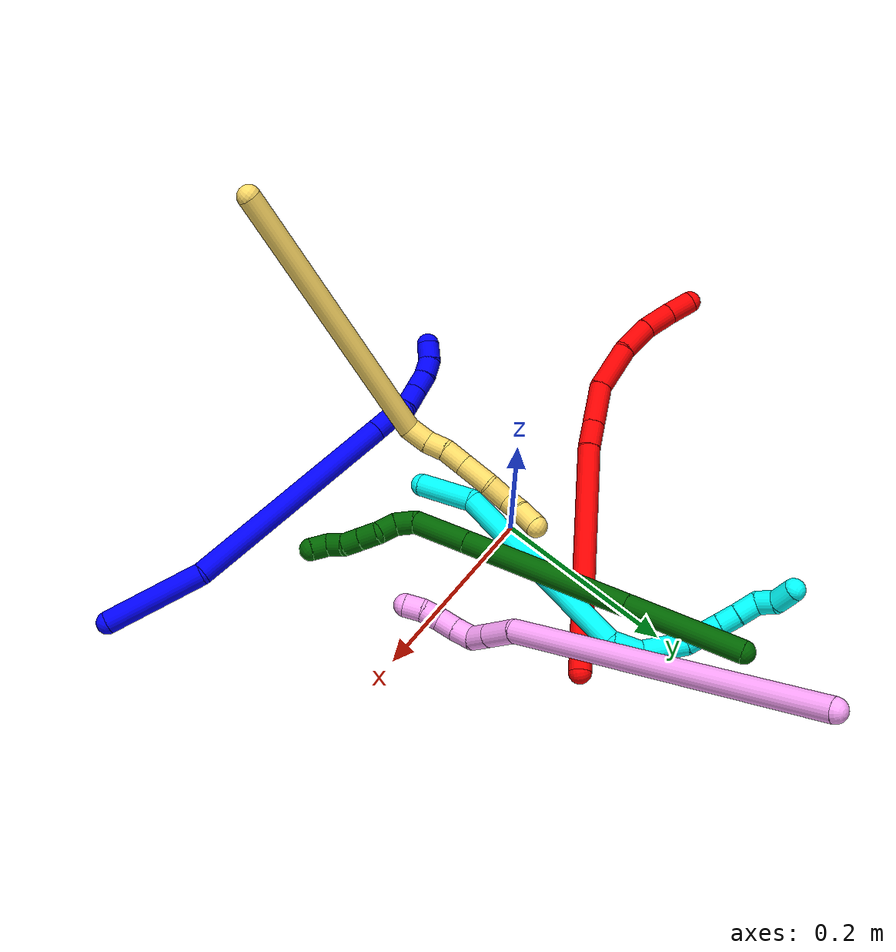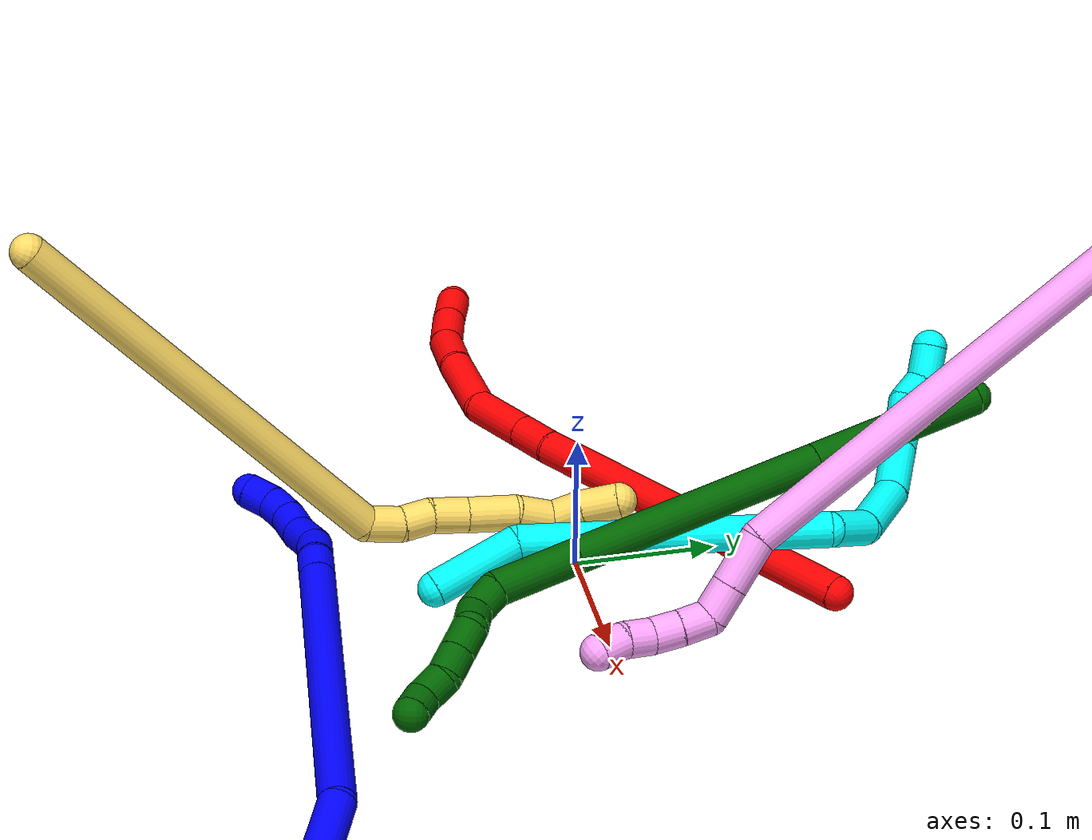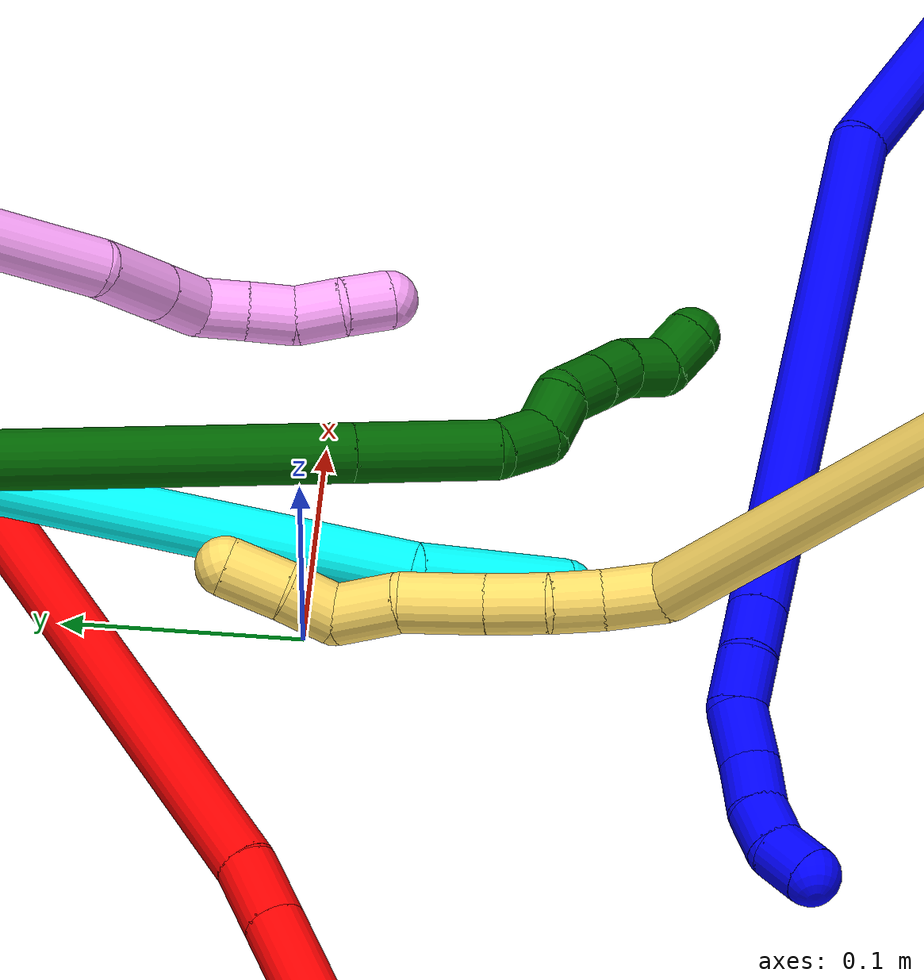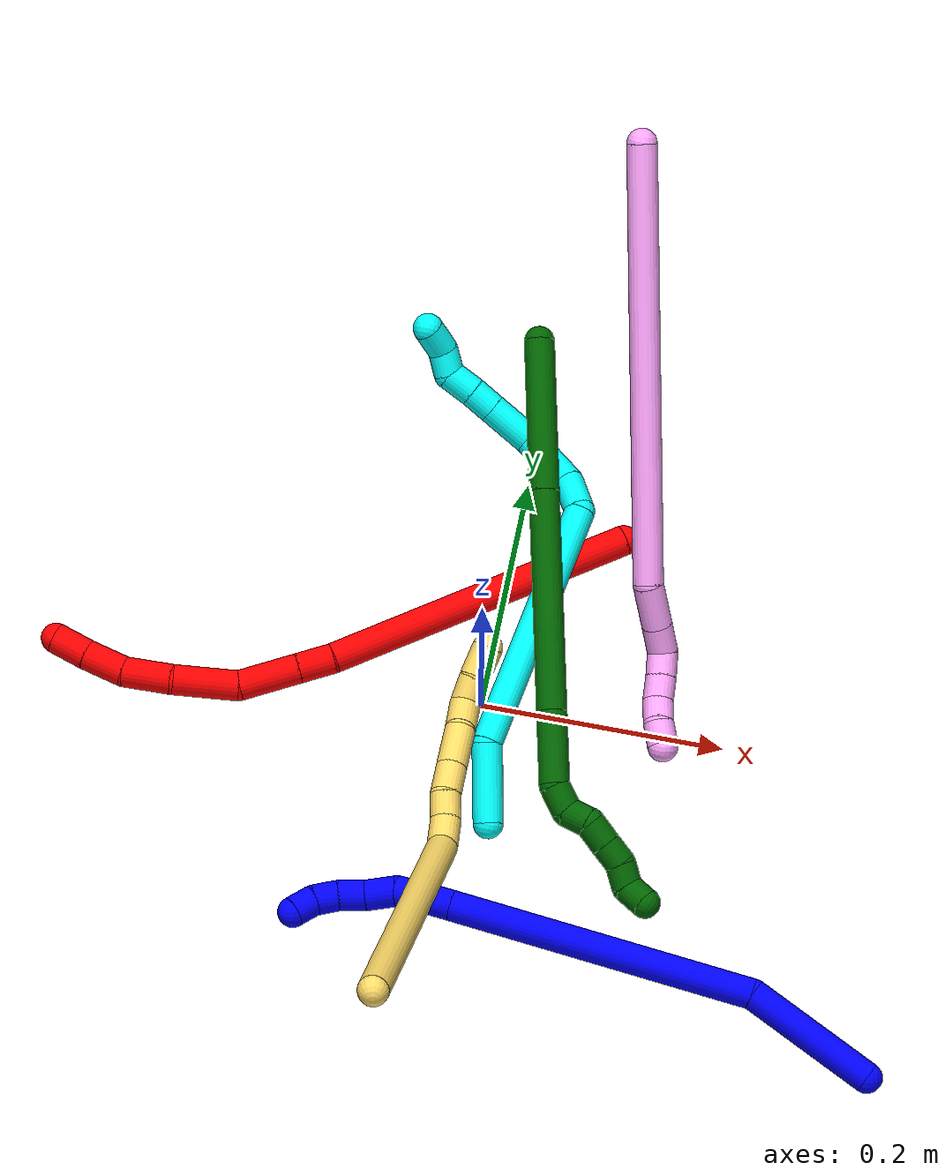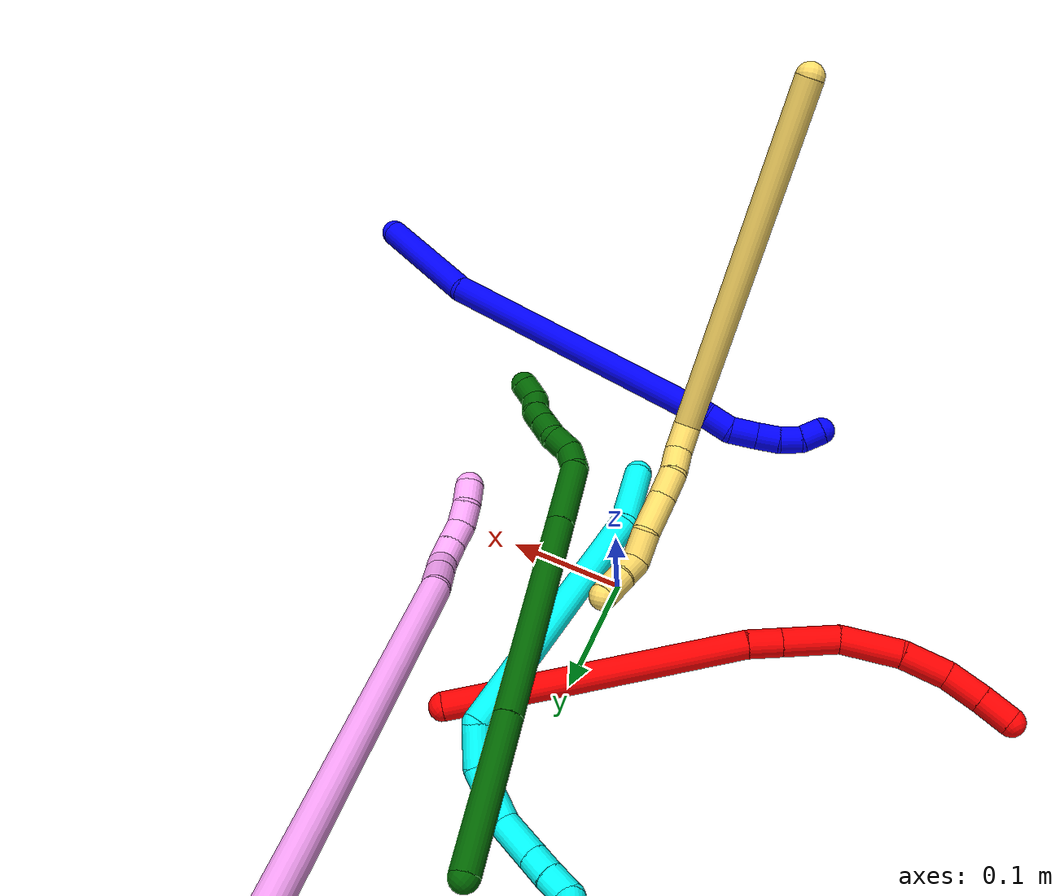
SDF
<sdf version="1.7">
 <world name="default">
  <plugin name="TubeGeneratorPlugin" filename="libtube_generator_plugin.so"/>
  <model name="photoneo_s_sensor">
   <static>1</static>
   <pose>0 0 2 1.57079 1.57079 3.14159</pose>
   <link name="link">
    <inertial><mass>0.1</mass></inertial>
    <sensor name="sensor" type="depth">
     <update_rate>30</update_rate>
     <camera>
      <horizontal_fov>1.22</horizontal_fov>
      <image><width>1920</width><height>1200</height><format>B8G8R8</format></image>
      <clip><near>0.1</near><far>4</far></clip>
      <depth_camera><output>points</output></depth_camera>
     </camera>
     <plugin name="camera_plugin" filename="libgazebo_ros_depth_camera.so">
      <baseline>0.2</baseline>
      <alwaysOn>1</alwaysOn>
      <updateRate>0.0</updateRate>
      <cameraName>camera_ir</cameraName>
      <imageTopicName>/camera/color/image_raw</imageTopicName>
      <cameraInfoTopicName>/camera/color/camera_info</cameraInfoTopicName>
      <depthImageTopicName>/camera/depth/image_raw</depthImageTopicName>
      <depthImageCameraInfoTopicName>/camera/depth/camera_info</depthImageCameraInfoTopicName>
      <pointCloudTopicName>/camera/depth/points</pointCloudTopicName>
      <frameName>fr_optical</frameName>
      <pointCloudCutoff>0.1</pointCloudCutoff>
      <pointCloudCutoffMax>2.0</pointCloudCutoffMax>
      <distortionK1>0</distortionK1>
      <distortionK2>0</distortionK2>
      <distortionK3>0</distortionK3>
      <distortionT1>0</distortionT1>
      <distortionT2>0</distortionT2>
      <CxPrime>0</CxPrime>
      <Cx>0</Cx>
      <Cy>0</Cy>
      <focalLength>0</focalLength>
      <hackBaseline>0</hackBaseline>
     </plugin>
    </sensor>
   </link>
  </model>
  <gravity>0 0 -9.8</gravity>
  <magnetic_field>6e-06 2.3e-05 -4.2e-05</magnetic_field>
  <atmosphere type="adiabatic"/>
  <physics name="default_physics" default="0" type="ode">
   <max_step_size>0.003</max_step_size>
   <real_time_factor>1</real_time_factor>
   <real_time_update_rate>1000</real_time_update_rate>
   <max_contacts>10000</max_contacts>
   <ode>
    <solver>
     <type>quick</type>
     <iters>100</iters>
     <sor>1.3</sor>
     <use_dynamic_moi_rescaling>0</use_dynamic_moi_rescaling>
    </solver>
    <constraints>
     <contact_max_correcting_vel>0</contact_max_correcting_vel>
     <contact_surface_layer>0.001</contact_surface_layer>
     <cfm>0</cfm>
     <erp>0.2</erp>
    </constraints>
   </ode>
  </physics>
  <scene><ambient>0.4 0.4 0.4 1</ambient><background>0.7 0.7 0.7 1</background><shadows>0</shadows></scene>
  <audio><device>default</device></audio>
  <spherical_coordinates>
   <surface_model>EARTH_WGS84</surface_model>
   <latitude_deg>0</latitude_deg>
   <longitude_deg>0</longitude_deg>
   <elevation>0</elevation>
   <heading_deg>0</heading_deg>
  </spherical_coordinates>
  <model name="bin">
   <static>1</static>
   <link name="bottom">
    <collision name="collision-bottom">
     <pose>0 0 -0.01 0 -0 0</pose>
     <geometry><box><size>0.8 0.6 0.02</size></box></geometry>
     <surface>
      <friction><ode><mu>100</mu><mu2>100</mu2></ode></friction>
      <contact><collide_bitmask>65535</collide_bitmask></contact>
     </surface>
    </collision>
   </link>
   <link name="west_wall">
    <collision name="collision-west_wall">
     <pose>-0.41 0 0.1 0 -0 0</pose>
     <geometry><box><size>0.02 0.6 0.2</size></box></geometry>
     <surface>
      <friction><ode><mu>100</mu><mu2>100</mu2></ode></friction>
      <contact><collide_bitmask>65535</collide_bitmask></contact>
     </surface>
    </collision>
   </link>
   <link name="east_wall">
    <collision name="collision-east_wall">
     <pose>0.41 0 0.1 0 -0 0</pose>
     <geometry><box><size>0.02 0.6 0.2</size></box></geometry>
     <surface>
      <friction><ode><mu>100</mu><mu2>100</mu2></ode></friction>
      <contact><collide_bitmask>65535</collide_bitmask></contact>
     </surface>
    </collision>
   </link>
   <link name="south_wall">
    <collision name="collision-south_wall">
     <pose>0 -0.31 0.1 0 -0 0</pose>
     <geometry><box><size>0.8 0.02 0.2</size></box></geometry>
     <surface>
      <friction><ode><mu>100</mu><mu2>100</mu2></ode></friction>
      <contact><collide_bitmask>65535</collide_bitmask></contact>
     </surface>
    </collision>
   </link>
   <link name="north_wall">
    <collision name="collision-north_wall">
     <pose>0 0.31 0.1 0 -0 0</pose>
     <geometry><box><size>0.8 0.02 0.2</size></box></geometry>
     <surface>
      <friction><ode><mu>100</mu><mu2>100</mu2></ode></friction>
      <contact><collide_bitmask>65535</collide_bitmask></contact>
     </surface>
    </collision>
   </link>
  </model>
  <model name="1">
   <static>0</static>
   <link name="1">
    <collision name="collision-cylinder-e_1_1_4">
     <pose>-0.034227 -0.004845 -0.044268 3.03258 -0.655284 -2.82325</pose>
     <geometry><cylinder><radius>0.0125</radius><length>0.112332</length></cylinder></geometry>
     <surface>
      <friction><ode><mu>1.16</mu><mu2>1.16</mu2><slip1>0</slip1><slip2>0</slip2></ode></friction>
      <contact><ode><kp>1e+06</kp><kd>1</kd><max_vel>0</max_vel><min_depth>0.001</min_depth></ode></contact>
     </surface>
    </collision>
    <visual name="visual-cylinder-e_1_1_4">
     <pose>-0.034227 -0.004845 -0.044268 3.03258 -0.655284 -2.82325</pose>
     <geometry><cylinder><radius>0.0125</radius><length>0.112332</length></cylinder></geometry>
     <material><ambient>0 0 1 1</ambient></material>
    </visual>
    <collision name="collision-cylinder-e_2_4_5">
     <pose>-0.110835 -0.000131 -0.207225 -3.06122 -0.341947 2.68399</pose>
     <geometry><cylinder><radius>0.0125</radius><length>0.25278</length></cylinder></geometry>
     <surface>
      <friction><ode><mu>1.16</mu><mu2>1.16</mu2><slip1>0</slip1><slip2>0</slip2></ode></friction>
      <contact><ode><kp>1e+06</kp><kd>1</kd><max_vel>0</max_vel><min_depth>0.001</min_depth></ode></contact>
     </surface>
    </collision>
    <visual name="visual-cylinder-e_2_4_5">
     <pose>-0.110835 -0.000131 -0.207225 -3.06122 -0.341947 2.68399</pose>
     <geometry><cylinder><radius>0.0125</radius><length>0.25278</length></cylinder></geometry>
     <material><ambient>0 0 1 1</ambient></material>
    </visual>
    <collision name="collision-cylinder-e_3_5_6">
     <pose>-0.156997 0.0101 -0.336649 -3.07926 -0.337997 2.78016</pose>
     <geometry><cylinder><radius>0.0125</radius><length>0.022804</length></cylinder></geometry>
     <surface>
      <friction><ode><mu>1.16</mu><mu2>1.16</mu2><slip1>0</slip1><slip2>0</slip2></ode></friction>
      <contact><ode><kp>1e+06</kp><kd>1</kd><max_vel>0</max_vel><min_depth>0.001</min_depth></ode></contact>
     </surface>
    </collision>
    <visual name="visual-cylinder-e_3_5_6">
     <pose>-0.156997 0.0101 -0.336649 -3.07926 -0.337997 2.78016</pose>
     <geometry><cylinder><radius>0.0125</radius><length>0.022804</length></cylinder></geometry>
     <material><ambient>0 0 1 1</ambient></material>
    </visual>
    <collision name="collision-cylinder-e_4_6_7">
     <pose>-0.164621 0.013742 -0.358194 -2.87326 -0.330274 1.78007</pose>
     <geometry><cylinder><radius>0.0125</radius><length>0.023702</length></cylinder></geometry>
     <surface>
      <friction><ode><mu>1.16</mu><mu2>1.16</mu2><slip1>0</slip1><slip2>0</slip2></ode></friction>
      <contact><ode><kp>1e+06</kp><kd>1</kd><max_vel>0</max_vel><min_depth>0.001</min_depth></ode></contact>
     </surface>
    </collision>
    <visual name="visual-cylinder-e_4_6_7">
     <pose>-0.164621 0.013742 -0.358194 -2.87326 -0.330274 1.78007</pose>
     <geometry><cylinder><radius>0.0125</radius><length>0.023702</length></cylinder></geometry>
     <material><ambient>0 0 1 1</ambient></material>
    </visual>
    <collision name="collision-cylinder-e_5_7_8">
     <pose>-0.16768 0.01943 -0.381578 -2.92882 0.060899 -0.555706</pose>
     <geometry><cylinder><radius>0.0125</radius><length>0.025776</length></cylinder></geometry>
     <surface>
      <friction><ode><mu>1.16</mu><mu2>1.16</mu2><slip1>0</slip1><slip2>0</slip2></ode></friction>
      <contact><ode><kp>1e+06</kp><kd>1</kd><max_vel>0</max_vel><min_depth>0.001</min_depth></ode></contact>
     </surface>
    </collision>
    <visual name="visual-cylinder-e_5_7_8">
     <pose>-0.16768 0.01943 -0.381578 -2.92882 0.060899 -0.555706</pose>
     <geometry><cylinder><radius>0.0125</radius><length>0.025776</length></cylinder></geometry>
     <material><ambient>0 0 1 1</ambient></material>
    </visual>
    <collision name="collision-cylinder-e_6_8_9">
     <pose>-0.167195 0.022464 -0.405319 -3.11317 -0.026804 1.51223</pose>
     <geometry><cylinder><radius>0.0125</radius><length>0.022351</length></cylinder></geometry>
     <surface>
      <friction><ode><mu>1.16</mu><mu2>1.16</mu2><slip1>0</slip1><slip2>0</slip2></ode></friction>
      <contact><ode><kp>1e+06</kp><kd>1</kd><max_vel>0</max_vel><min_depth>0.001</min_depth></ode></contact>
     </surface>
    </collision>
    <visual name="visual-cylinder-e_6_8_9">
     <pose>-0.167195 0.022464 -0.405319 -3.11317 -0.026804 1.51223</pose>
     <geometry><cylinder><radius>0.0125</radius><length>0.022351</length></cylinder></geometry>
     <material><ambient>0 0 1 1</ambient></material>
    </visual>
    <collision name="collision-cylinder-e_7_9_10">
     <pose>-0.165621 0.022345 -0.426383 3.09752 0.186944 2.67977</pose>
     <geometry><cylinder><radius>0.0125</radius><length>0.020166</length></cylinder></geometry>
     <surface>
      <friction><ode><mu>1.16</mu><mu2>1.16</mu2><slip1>0</slip1><slip2>0</slip2></ode></friction>
      <contact><ode><kp>1e+06</kp><kd>1</kd><max_vel>0</max_vel><min_depth>0.001</min_depth></ode></contact>
     </surface>
    </collision>
    <visual name="visual-cylinder-e_7_9_10">
     <pose>-0.165621 0.022345 -0.426383 3.09752 0.186944 2.67977</pose>
     <geometry><cylinder><radius>0.0125</radius><length>0.020166</length></cylinder></geometry>
     <material><ambient>0 0 1 1</ambient></material>
    </visual>
    <collision name="collision-cylinder-e_8_10_2">
     <pose>-0.158561 0.020172 -0.444706 2.93833 0.542475 2.43859</pose>
     <geometry><cylinder><radius>0.0125</radius><length>0.020088</length></cylinder></geometry>
     <surface>
      <friction><ode><mu>1.16</mu><mu2>1.16</mu2><slip1>0</slip1><slip2>0</slip2></ode></friction>
      <contact><ode><kp>1e+06</kp><kd>1</kd><max_vel>0</max_vel><min_depth>0.001</min_depth></ode></contact>
     </surface>
    </collision>
    <visual name="visual-cylinder-e_8_10_2">
     <pose>-0.158561 0.020172 -0.444706 2.93833 0.542475 2.43859</pose>
     <geometry><cylinder><radius>0.0125</radius><length>0.020088</length></cylinder></geometry>
     <material><ambient>0 0 1 1</ambient></material>
    </visual>
    <collision name="collision-sphere-2">
     <pose>-0.153376 0.018436 -0.453131 0 -0 0</pose>
     <geometry><sphere><radius>0.0125</radius></sphere></geometry>
     <surface>
      <friction><ode><mu>1.16</mu><mu2>1.16</mu2><slip1>0</slip1><slip2>0</slip2></ode></friction>
      <contact><ode><kp>1e+06</kp><kd>1</kd><max_vel>0</max_vel><min_depth>0.001</min_depth></ode></contact>
     </surface>
    </collision>
    <visual name="visual-sphere-2">
     <pose>-0.153376 0.018436 -0.453131 0 -0 0</pose>
     <geometry><sphere><radius>0.0125</radius></sphere></geometry>
     <material><ambient>0 0 1 1</ambient></material>
    </visual>
    <collision name="collision-sphere-10">
     <pose>-0.163747 0.021909 -0.436281 0 -0 0</pose>
     <geometry><sphere><radius>0.0125</radius></sphere></geometry>
     <surface>
      <friction><ode><mu>1.16</mu><mu2>1.16</mu2><slip1>0</slip1><slip2>0</slip2></ode></friction>
      <contact><ode><kp>1e+06</kp><kd>1</kd><max_vel>0</max_vel><min_depth>0.001</min_depth></ode></contact>
     </surface>
    </collision>
    <visual name="visual-sphere-10">
     <pose>-0.163747 0.021909 -0.436281 0 -0 0</pose>
     <geometry><sphere><radius>0.0125</radius></sphere></geometry>
     <material><ambient>0 0 1 1</ambient></material>
    </visual>
    <collision name="collision-sphere-9">
     <pose>-0.167495 0.022782 -0.416486 0 -0 0</pose>
     <geometry><sphere><radius>0.0125</radius></sphere></geometry>
     <surface>
      <friction><ode><mu>1.16</mu><mu2>1.16</mu2><slip1>0</slip1><slip2>0</slip2></ode></friction>
      <contact><ode><kp>1e+06</kp><kd>1</kd><max_vel>0</max_vel><min_depth>0.001</min_depth></ode></contact>
     </surface>
    </collision>
    <visual name="visual-sphere-9">
     <pose>-0.167495 0.022782 -0.416486 0 -0 0</pose>
     <geometry><sphere><radius>0.0125</radius></sphere></geometry>
     <material><ambient>0 0 1 1</ambient></material>
    </visual>
    <collision name="collision-sphere-4">
     <pose>-0.068453 -0.009691 -0.088537 0 -0 0</pose>
     <geometry><sphere><radius>0.0125</radius></sphere></geometry>
     <surface>
      <friction><ode><mu>1.16</mu><mu2>1.16</mu2><slip1>0</slip1><slip2>0</slip2></ode></friction>
      <contact><ode><kp>1e+06</kp><kd>1</kd><max_vel>0</max_vel><min_depth>0.001</min_depth></ode></contact>
     </surface>
    </collision>
    <visual name="visual-sphere-4">
     <pose>-0.068453 -0.009691 -0.088537 0 -0 0</pose>
     <geometry><sphere><radius>0.0125</radius></sphere></geometry>
     <material><ambient>0 0 1 1</ambient></material>
    </visual>
    <collision name="collision-sphere-1">
     <geometry><sphere><radius>0.0125</radius></sphere></geometry>
     <surface>
      <friction><ode><mu>1.16</mu><mu2>1.16</mu2><slip1>0</slip1><slip2>0</slip2></ode></friction>
      <contact><ode><kp>1e+06</kp><kd>1</kd><max_vel>0</max_vel><min_depth>0.001</min_depth></ode></contact>
     </surface>
    </collision>
    <visual name="visual-sphere-1">
     <geometry><sphere><radius>0.0125</radius></sphere></geometry>
     <material><ambient>0 0 1 1</ambient></material>
    </visual>
    <collision name="collision-sphere-8">
     <pose>-0.166896 0.022147 -0.394152 0 -0 0</pose>
     <geometry><sphere><radius>0.0125</radius></sphere></geometry>
     <surface>
      <friction><ode><mu>1.16</mu><mu2>1.16</mu2><slip1>0</slip1><slip2>0</slip2></ode></friction>
      <contact><ode><kp>1e+06</kp><kd>1</kd><max_vel>0</max_vel><min_depth>0.001</min_depth></ode></contact>
     </surface>
    </collision>
    <visual name="visual-sphere-8">
     <pose>-0.166896 0.022147 -0.394152 0 -0 0</pose>
     <geometry><sphere><radius>0.0125</radius></sphere></geometry>
     <material><ambient>0 0 1 1</ambient></material>
    </visual>
    <collision name="collision-sphere-5">
     <pose>-0.153216 0.00943 -0.325913 0 -0 0</pose>
     <geometry><sphere><radius>0.0125</radius></sphere></geometry>
     <surface>
      <friction><ode><mu>1.16</mu><mu2>1.16</mu2><slip1>0</slip1><slip2>0</slip2></ode></friction>
      <contact><ode><kp>1e+06</kp><kd>1</kd><max_vel>0</max_vel><min_depth>0.001</min_depth></ode></contact>
     </surface>
    </collision>
    <visual name="visual-sphere-5">
     <pose>-0.153216 0.00943 -0.325913 0 -0 0</pose>
     <geometry><sphere><radius>0.0125</radius></sphere></geometry>
     <material><ambient>0 0 1 1</ambient></material>
    </visual>
    <collision name="collision-sphere-6">
     <pose>-0.160778 0.01077 -0.347385 0 -0 0</pose>
     <geometry><sphere><radius>0.0125</radius></sphere></geometry>
     <surface>
      <friction><ode><mu>1.16</mu><mu2>1.16</mu2><slip1>0</slip1><slip2>0</slip2></ode></friction>
      <contact><ode><kp>1e+06</kp><kd>1</kd><max_vel>0</max_vel><min_depth>0.001</min_depth></ode></contact>
     </surface>
    </collision>
    <visual name="visual-sphere-6">
     <pose>-0.160778 0.01077 -0.347385 0 -0 0</pose>
     <geometry><sphere><radius>0.0125</radius></sphere></geometry>
     <material><ambient>0 0 1 1</ambient></material>
    </visual>
    <collision name="collision-sphere-7">
     <pose>-0.168465 0.016714 -0.369004 0 -0 0</pose>
     <geometry><sphere><radius>0.0125</radius></sphere></geometry>
     <surface>
      <friction><ode><mu>1.16</mu><mu2>1.16</mu2><slip1>0</slip1><slip2>0</slip2></ode></friction>
      <contact><ode><kp>1e+06</kp><kd>1</kd><max_vel>0</max_vel><min_depth>0.001</min_depth></ode></contact>
     </surface>
    </collision>
    <visual name="visual-sphere-7">
     <pose>-0.168465 0.016714 -0.369004 0 -0 0</pose>
     <geometry><sphere><radius>0.0125</radius></sphere></geometry>
     <material><ambient>0 0 1 1</ambient></material>
    </visual>
    <inertial>
     <pose>-0.107856 0.003675 -0.219897 0 -0 0</pose>
     <mass>0.5</mass>
     <inertia>
      <ixx>-0.000714</ixx>
      <ixy>0</ixy>
      <ixz>0</ixz>
      <iyy>0.001889</iyy>
      <iyz>0</iyz>
      <izz>0.000401</izz>
     </inertia>
    </inertial>
   </link>
   <pose>0.363833 -0.259538 0.012311 -1.59137 0.085326 -1.34274</pose>
  </model>
  <model name="2">
   <static>0</static>
   <link name="2">
    <collision name="collision-cylinder-e_1_1_4">
     <pose>-0.126874 0.00416 0.03083 -0.134109 -1.33034 0.105259</pose>
     <geometry><cylinder><radius>0.0125</radius><length>0.261264</length></cylinder></geometry>
     <surface>
      <friction><ode><mu>1.16</mu><mu2>1.16</mu2><slip1>0</slip1><slip2>0</slip2></ode></friction>
      <contact><ode><kp>1e+06</kp><kd>1</kd><max_vel>0</max_vel><min_depth>0.001</min_depth></ode></contact>
     </surface>
    </collision>
    <visual name="visual-cylinder-e_1_1_4">
     <pose>-0.126874 0.00416 0.03083 -0.134109 -1.33034 0.105259</pose>
     <geometry><cylinder><radius>0.0125</radius><length>0.261264</length></cylinder></geometry>
     <material><ambient>1 0 0 1</ambient></material>
    </visual>
    <collision name="collision-cylinder-e_2_4_5">
     <pose>-0.267495 0.009745 0.066961 -0.262749 -1.19091 0.178563</pose>
     <geometry><cylinder><radius>0.0125</radius><length>0.029606</length></cylinder></geometry>
     <surface>
      <friction><ode><mu>1.16</mu><mu2>1.16</mu2><slip1>0</slip1><slip2>0</slip2></ode></friction>
      <contact><ode><kp>1e+06</kp><kd>1</kd><max_vel>0</max_vel><min_depth>0.001</min_depth></ode></contact>
     </surface>
    </collision>
    <visual name="visual-cylinder-e_2_4_5">
     <pose>-0.267495 0.009745 0.066961 -0.262749 -1.19091 0.178563</pose>
     <geometry><cylinder><radius>0.0125</radius><length>0.029606</length></cylinder></geometry>
     <material><ambient>1 0 0 1</ambient></material>
    </visual>
    <collision name="collision-cylinder-e_3_5_6">
     <pose>-0.304763 0.013608 0.081335 -0.262448 -1.1908 0.178337</pose>
     <geometry><cylinder><radius>0.0125</radius><length>0.050655</length></cylinder></geometry>
     <surface>
      <friction><ode><mu>1.16</mu><mu2>1.16</mu2><slip1>0</slip1><slip2>0</slip2></ode></friction>
      <contact><ode><kp>1e+06</kp><kd>1</kd><max_vel>0</max_vel><min_depth>0.001</min_depth></ode></contact>
     </surface>
    </collision>
    <visual name="visual-cylinder-e_3_5_6">
     <pose>-0.304763 0.013608 0.081335 -0.262448 -1.1908 0.178337</pose>
     <geometry><cylinder><radius>0.0125</radius><length>0.050655</length></cylinder></geometry>
     <material><ambient>1 0 0 1</ambient></material>
    </visual>
    <collision name="collision-cylinder-e_4_6_7">
     <pose>-0.34835 0.015873 0.108447 0.009557 -0.838497 -0.004259</pose>
     <geometry><cylinder><radius>0.0125</radius><length>0.053968</length></cylinder></geometry>
     <surface>
      <friction><ode><mu>1.16</mu><mu2>1.16</mu2><slip1>0</slip1><slip2>0</slip2></ode></friction>
      <contact><ode><kp>1e+06</kp><kd>1</kd><max_vel>0</max_vel><min_depth>0.001</min_depth></ode></contact>
     </surface>
    </collision>
    <visual name="visual-cylinder-e_4_6_7">
     <pose>-0.34835 0.015873 0.108447 0.009557 -0.838497 -0.004259</pose>
     <geometry><cylinder><radius>0.0125</radius><length>0.053968</length></cylinder></geometry>
     <material><ambient>1 0 0 1</ambient></material>
    </visual>
    <collision name="collision-cylinder-e_5_7_8">
     <pose>-0.381354 0.019285 0.141872 -0.228925 -0.686215 0.082093</pose>
     <geometry><cylinder><radius>0.0125</radius><length>0.040838</length></cylinder></geometry>
     <surface>
      <friction><ode><mu>1.16</mu><mu2>1.16</mu2><slip1>0</slip1><slip2>0</slip2></ode></friction>
      <contact><ode><kp>1e+06</kp><kd>1</kd><max_vel>0</max_vel><min_depth>0.001</min_depth></ode></contact>
     </surface>
    </collision>
    <visual name="visual-cylinder-e_5_7_8">
     <pose>-0.381354 0.019285 0.141872 -0.228925 -0.686215 0.082093</pose>
     <geometry><cylinder><radius>0.0125</radius><length>0.040838</length></cylinder></geometry>
     <material><ambient>1 0 0 1</ambient></material>
    </visual>
    <collision name="collision-cylinder-e_6_8_9">
     <pose>-0.401718 0.024272 0.172525 -0.091559 -0.451069 0.021021</pose>
     <geometry><cylinder><radius>0.0125</radius><length>0.034071</length></cylinder></geometry>
     <surface>
      <friction><ode><mu>1.16</mu><mu2>1.16</mu2><slip1>0</slip1><slip2>0</slip2></ode></friction>
      <contact><ode><kp>1e+06</kp><kd>1</kd><max_vel>0</max_vel><min_depth>0.001</min_depth></ode></contact>
     </surface>
    </collision>
    <visual name="visual-cylinder-e_6_8_9">
     <pose>-0.401718 0.024272 0.172525 -0.091559 -0.451069 0.021021</pose>
     <geometry><cylinder><radius>0.0125</radius><length>0.034071</length></cylinder></geometry>
     <material><ambient>1 0 0 1</ambient></material>
    </visual>
    <collision name="collision-cylinder-e_7_9_2">
     <pose>-0.41476 0.02673 0.201444 -0.077252 -0.389196 0.015233</pose>
     <geometry><cylinder><radius>0.0125</radius><length>0.029599</length></cylinder></geometry>
     <surface>
      <friction><ode><mu>1.16</mu><mu2>1.16</mu2><slip1>0</slip1><slip2>0</slip2></ode></friction>
      <contact><ode><kp>1e+06</kp><kd>1</kd><max_vel>0</max_vel><min_depth>0.001</min_depth></ode></contact>
     </surface>
    </collision>
    <visual name="visual-cylinder-e_7_9_2">
     <pose>-0.41476 0.02673 0.201444 -0.077252 -0.389196 0.015233</pose>
     <geometry><cylinder><radius>0.0125</radius><length>0.029599</length></cylinder></geometry>
     <material><ambient>1 0 0 1</ambient></material>
    </visual>
    <collision name="collision-sphere-2">
     <pose>-0.420375 0.027787 0.215096 0 -0 0</pose>
     <geometry><sphere><radius>0.0125</radius></sphere></geometry>
     <surface>
      <friction><ode><mu>1.16</mu><mu2>1.16</mu2><slip1>0</slip1><slip2>0</slip2></ode></friction>
      <contact><ode><kp>1e+06</kp><kd>1</kd><max_vel>0</max_vel><min_depth>0.001</min_depth></ode></contact>
     </surface>
    </collision>
    <visual name="visual-sphere-2">
     <pose>-0.420375 0.027787 0.215096 0 -0 0</pose>
     <geometry><sphere><radius>0.0125</radius></sphere></geometry>
     <material><ambient>1 0 0 1</ambient></material>
    </visual>
    <collision name="collision-sphere-9">
     <pose>-0.409144 0.025674 0.187792 0 -0 0</pose>
     <geometry><sphere><radius>0.0125</radius></sphere></geometry>
     <surface>
      <friction><ode><mu>1.16</mu><mu2>1.16</mu2><slip1>0</slip1><slip2>0</slip2></ode></friction>
      <contact><ode><kp>1e+06</kp><kd>1</kd><max_vel>0</max_vel><min_depth>0.001</min_depth></ode></contact>
     </surface>
    </collision>
    <visual name="visual-sphere-9">
     <pose>-0.409144 0.025674 0.187792 0 -0 0</pose>
     <geometry><sphere><radius>0.0125</radius></sphere></geometry>
     <material><ambient>1 0 0 1</ambient></material>
    </visual>
    <collision name="collision-sphere-4">
     <pose>-0.253747 0.008319 0.06166 0 -0 0</pose>
     <geometry><sphere><radius>0.0125</radius></sphere></geometry>
     <surface>
      <friction><ode><mu>1.16</mu><mu2>1.16</mu2><slip1>0</slip1><slip2>0</slip2></ode></friction>
      <contact><ode><kp>1e+06</kp><kd>1</kd><max_vel>0</max_vel><min_depth>0.001</min_depth></ode></contact>
     </surface>
    </collision>
    <visual name="visual-sphere-4">
     <pose>-0.253747 0.008319 0.06166 0 -0 0</pose>
     <geometry><sphere><radius>0.0125</radius></sphere></geometry>
     <material><ambient>1 0 0 1</ambient></material>
    </visual>
    <collision name="collision-sphere-1">
     <geometry><sphere><radius>0.0125</radius></sphere></geometry>
     <surface>
      <friction><ode><mu>1.16</mu><mu2>1.16</mu2><slip1>0</slip1><slip2>0</slip2></ode></friction>
      <contact><ode><kp>1e+06</kp><kd>1</kd><max_vel>0</max_vel><min_depth>0.001</min_depth></ode></contact>
     </surface>
    </collision>
    <visual name="visual-sphere-1">
     <geometry><sphere><radius>0.0125</radius></sphere></geometry>
     <material><ambient>1 0 0 1</ambient></material>
    </visual>
    <collision name="collision-sphere-8">
     <pose>-0.394292 0.02287 0.157257 0 -0 0</pose>
     <geometry><sphere><radius>0.0125</radius></sphere></geometry>
     <surface>
      <friction><ode><mu>1.16</mu><mu2>1.16</mu2><slip1>0</slip1><slip2>0</slip2></ode></friction>
      <contact><ode><kp>1e+06</kp><kd>1</kd><max_vel>0</max_vel><min_depth>0.001</min_depth></ode></contact>
     </surface>
    </collision>
    <visual name="visual-sphere-8">
     <pose>-0.394292 0.02287 0.157257 0 -0 0</pose>
     <geometry><sphere><radius>0.0125</radius></sphere></geometry>
     <material><ambient>1 0 0 1</ambient></material>
    </visual>
    <collision name="collision-sphere-5">
     <pose>-0.281242 0.011171 0.072262 0 -0 0</pose>
     <geometry><sphere><radius>0.0125</radius></sphere></geometry>
     <surface>
      <friction><ode><mu>1.16</mu><mu2>1.16</mu2><slip1>0</slip1><slip2>0</slip2></ode></friction>
      <contact><ode><kp>1e+06</kp><kd>1</kd><max_vel>0</max_vel><min_depth>0.001</min_depth></ode></contact>
     </surface>
    </collision>
    <visual name="visual-sphere-5">
     <pose>-0.281242 0.011171 0.072262 0 -0 0</pose>
     <geometry><sphere><radius>0.0125</radius></sphere></geometry>
     <material><ambient>1 0 0 1</ambient></material>
    </visual>
    <collision name="collision-sphere-6">
     <pose>-0.328284 0.016045 0.090407 0 -0 0</pose>
     <geometry><sphere><radius>0.0125</radius></sphere></geometry>
     <surface>
      <friction><ode><mu>1.16</mu><mu2>1.16</mu2><slip1>0</slip1><slip2>0</slip2></ode></friction>
      <contact><ode><kp>1e+06</kp><kd>1</kd><max_vel>0</max_vel><min_depth>0.001</min_depth></ode></contact>
     </surface>
    </collision>
    <visual name="visual-sphere-6">
     <pose>-0.328284 0.016045 0.090407 0 -0 0</pose>
     <geometry><sphere><radius>0.0125</radius></sphere></geometry>
     <material><ambient>1 0 0 1</ambient></material>
    </visual>
    <collision name="collision-sphere-7">
     <pose>-0.368416 0.0157 0.126487 0 -0 0</pose>
     <geometry><sphere><radius>0.0125</radius></sphere></geometry>
     <surface>
      <friction><ode><mu>1.16</mu><mu2>1.16</mu2><slip1>0</slip1><slip2>0</slip2></ode></friction>
      <contact><ode><kp>1e+06</kp><kd>1</kd><max_vel>0</max_vel><min_depth>0.001</min_depth></ode></contact>
     </surface>
    </collision>
    <visual name="visual-sphere-7">
     <pose>-0.368416 0.0157 0.126487 0 -0 0</pose>
     <geometry><sphere><radius>0.0125</radius></sphere></geometry>
     <material><ambient>1 0 0 1</ambient></material>
    </visual>
    <inertial>
     <pose>-0.233683 0.010654 0.075289 0 -0 0</pose>
     <mass>0.5</mass>
     <inertia>
      <ixx>0.000389</ixx>
      <ixy>0</ixy>
      <ixz>0</ixz>
      <iyy>0.001583</iyy>
      <iyz>0</iyz>
      <izz>0.001453</izz>
     </inertia>
    </inertial>
   </link>
   <pose>0.086918 0.162267 0.01149 -1.49866 0.03196 0.85929</pose>
  </model>
  <model name="3">
   <static>0</static>
   <link name="3">
    <collision name="collision-cylinder-e_1_1_4">
     <pose>-0.006513 0.004417 0.031629 -0.138763 -0.201174 0.014027</pose>
     <geometry><cylinder><radius>0.0125</radius><length>0.065187</length></cylinder></geometry>
     <surface>
      <friction><ode><mu>1.16</mu><mu2>1.16</mu2><slip1>0</slip1><slip2>0</slip2></ode></friction>
      <contact><ode><kp>1e+06</kp><kd>1</kd><max_vel>0</max_vel><min_depth>0.001</min_depth></ode></contact>
     </surface>
    </collision>
    <visual name="visual-cylinder-e_1_1_4">
     <pose>-0.006513 0.004417 0.031629 -0.138763 -0.201174 0.014027</pose>
     <geometry><cylinder><radius>0.0125</radius><length>0.065187</length></cylinder></geometry>
     <material><ambient>0.003922 1 0.996078 1</ambient></material>
    </visual>
    <collision name="collision-cylinder-e_2_4_5">
     <pose>0.009282 0.049785 0.161273 -0.395752 0.206992 -0.041645</pose>
     <geometry><cylinder><radius>0.0125</radius><length>0.217084</length></cylinder></geometry>
     <surface>
      <friction><ode><mu>1.16</mu><mu2>1.16</mu2><slip1>0</slip1><slip2>0</slip2></ode></friction>
      <contact><ode><kp>1e+06</kp><kd>1</kd><max_vel>0</max_vel><min_depth>0.001</min_depth></ode></contact>
     </surface>
    </collision>
    <visual name="visual-cylinder-e_2_4_5">
     <pose>0.009282 0.049785 0.161273 -0.395752 0.206992 -0.041645</pose>
     <geometry><cylinder><radius>0.0125</radius><length>0.217084</length></cylinder></geometry>
     <material><ambient>0.003922 1 0.996078 1</ambient></material>
    </visual>
    <collision name="collision-cylinder-e_3_5_6">
     <pose>0.025877 0.103856 0.269974 -0.887317 -0.325511 0.155767</pose>
     <geometry><cylinder><radius>0.0125</radius><length>0.035721</length></cylinder></geometry>
     <surface>
      <friction><ode><mu>1.16</mu><mu2>1.16</mu2><slip1>0</slip1><slip2>0</slip2></ode></friction>
      <contact><ode><kp>1e+06</kp><kd>1</kd><max_vel>0</max_vel><min_depth>0.001</min_depth></ode></contact>
     </surface>
    </collision>
    <visual name="visual-cylinder-e_3_5_6">
     <pose>0.025877 0.103856 0.269974 -0.887317 -0.325511 0.155767</pose>
     <geometry><cylinder><radius>0.0125</radius><length>0.035721</length></cylinder></geometry>
     <material><ambient>0.003922 1 0.996078 1</ambient></material>
    </visual>
    <collision name="collision-cylinder-e_4_6_7">
     <pose>0.001812 0.127265 0.294209 -0.649434 -0.823343 0.291871</pose>
     <geometry><cylinder><radius>0.0125</radius><length>0.05005</length></cylinder></geometry>
     <surface>
      <friction><ode><mu>1.16</mu><mu2>1.16</mu2><slip1>0</slip1><slip2>0</slip2></ode></friction>
      <contact><ode><kp>1e+06</kp><kd>1</kd><max_vel>0</max_vel><min_depth>0.001</min_depth></ode></contact>
     </surface>
    </collision>
    <visual name="visual-cylinder-e_4_6_7">
     <pose>0.001812 0.127265 0.294209 -0.649434 -0.823343 0.291871</pose>
     <geometry><cylinder><radius>0.0125</radius><length>0.05005</length></cylinder></geometry>
     <material><ambient>0.003922 1 0.996078 1</ambient></material>
    </visual>
    <collision name="collision-cylinder-e_5_7_8">
     <pose>-0.034211 0.138066 0.317517 -0.052553 -1.06556 0.030993</pose>
     <geometry><cylinder><radius>0.0125</radius><length>0.040384</length></cylinder></geometry>
     <surface>
      <friction><ode><mu>1.16</mu><mu2>1.16</mu2><slip1>0</slip1><slip2>0</slip2></ode></friction>
      <contact><ode><kp>1e+06</kp><kd>1</kd><max_vel>0</max_vel><min_depth>0.001</min_depth></ode></contact>
     </surface>
    </collision>
    <visual name="visual-cylinder-e_5_7_8">
     <pose>-0.034211 0.138066 0.317517 -0.052553 -1.06556 0.030993</pose>
     <geometry><cylinder><radius>0.0125</radius><length>0.040384</length></cylinder></geometry>
     <material><ambient>0.003922 1 0.996078 1</ambient></material>
    </visual>
    <collision name="collision-cylinder-e_6_8_9">
     <pose>-0.061149 0.138706 0.332484 -0.024433 -1.05883 0.014297</pose>
     <geometry><cylinder><radius>0.0125</radius><length>0.021264</length></cylinder></geometry>
     <surface>
      <friction><ode><mu>1.16</mu><mu2>1.16</mu2><slip1>0</slip1><slip2>0</slip2></ode></friction>
      <contact><ode><kp>1e+06</kp><kd>1</kd><max_vel>0</max_vel><min_depth>0.001</min_depth></ode></contact>
     </surface>
    </collision>
    <visual name="visual-cylinder-e_6_8_9">
     <pose>-0.061149 0.138706 0.332484 -0.024433 -1.05883 0.014297</pose>
     <geometry><cylinder><radius>0.0125</radius><length>0.021264</length></cylinder></geometry>
     <material><ambient>0.003922 1 0.996078 1</ambient></material>
    </visual>
    <collision name="collision-cylinder-e_7_9_10">
     <pose>-0.081386 0.139291 0.342935 -0.087084 -1.12328 0.054817</pose>
     <geometry><cylinder><radius>0.0125</radius><length>0.024333</length></cylinder></geometry>
     <surface>
      <friction><ode><mu>1.16</mu><mu2>1.16</mu2><slip1>0</slip1><slip2>0</slip2></ode></friction>
      <contact><ode><kp>1e+06</kp><kd>1</kd><max_vel>0</max_vel><min_depth>0.001</min_depth></ode></contact>
     </surface>
    </collision>
    <visual name="visual-cylinder-e_7_9_10">
     <pose>-0.081386 0.139291 0.342935 -0.087084 -1.12328 0.054817</pose>
     <geometry><cylinder><radius>0.0125</radius><length>0.024333</length></cylinder></geometry>
     <material><ambient>0.003922 1 0.996078 1</ambient></material>
    </visual>
    <collision name="collision-cylinder-e_8_10_11">
     <pose>-0.096954 0.138626 0.357617 0.118508 -0.450748 -0.0272</pose>
     <geometry><cylinder><radius>0.0125</radius><length>0.021115</length></cylinder></geometry>
     <surface>
      <friction><ode><mu>1.16</mu><mu2>1.16</mu2><slip1>0</slip1><slip2>0</slip2></ode></friction>
      <contact><ode><kp>1e+06</kp><kd>1</kd><max_vel>0</max_vel><min_depth>0.001</min_depth></ode></contact>
     </surface>
    </collision>
    <visual name="visual-cylinder-e_8_10_11">
     <pose>-0.096954 0.138626 0.357617 0.118508 -0.450748 -0.0272</pose>
     <geometry><cylinder><radius>0.0125</radius><length>0.021115</length></cylinder></geometry>
     <material><ambient>0.003922 1 0.996078 1</ambient></material>
    </visual>
    <collision name="collision-cylinder-e_9_11_2">
     <pose>-0.109632 0.131662 0.37448 0.66636 -0.707441 -0.254204</pose>
     <geometry><cylinder><radius>0.0125</radius><length>0.024862</length></cylinder></geometry>
     <surface>
      <friction><ode><mu>1.16</mu><mu2>1.16</mu2><slip1>0</slip1><slip2>0</slip2></ode></friction>
      <contact><ode><kp>1e+06</kp><kd>1</kd><max_vel>0</max_vel><min_depth>0.001</min_depth></ode></contact>
     </surface>
    </collision>
    <visual name="visual-cylinder-e_9_11_2">
     <pose>-0.109632 0.131662 0.37448 0.66636 -0.707441 -0.254204</pose>
     <geometry><cylinder><radius>0.0125</radius><length>0.024862</length></cylinder></geometry>
     <material><ambient>0.003922 1 0.996078 1</ambient></material>
    </visual>
    <collision name="collision-sphere-2">
     <pose>-0.117711 0.125822 0.381907 0 -0 0</pose>
     <geometry><sphere><radius>0.0125</radius></sphere></geometry>
     <surface>
      <friction><ode><mu>1.16</mu><mu2>1.16</mu2><slip1>0</slip1><slip2>0</slip2></ode></friction>
      <contact><ode><kp>1e+06</kp><kd>1</kd><max_vel>0</max_vel><min_depth>0.001</min_depth></ode></contact>
     </surface>
    </collision>
    <visual name="visual-sphere-2">
     <pose>-0.117711 0.125822 0.381907 0 -0 0</pose>
     <geometry><sphere><radius>0.0125</radius></sphere></geometry>
     <material><ambient>0.003922 1 0.996078 1</ambient></material>
    </visual>
    <collision name="collision-sphere-11">
     <pose>-0.101553 0.137502 0.367053 0 -0 0</pose>
     <geometry><sphere><radius>0.0125</radius></sphere></geometry>
     <surface>
      <friction><ode><mu>1.16</mu><mu2>1.16</mu2><slip1>0</slip1><slip2>0</slip2></ode></friction>
      <contact><ode><kp>1e+06</kp><kd>1</kd><max_vel>0</max_vel><min_depth>0.001</min_depth></ode></contact>
     </surface>
    </collision>
    <visual name="visual-sphere-11">
     <pose>-0.101553 0.137502 0.367053 0 -0 0</pose>
     <geometry><sphere><radius>0.0125</radius></sphere></geometry>
     <material><ambient>0.003922 1 0.996078 1</ambient></material>
    </visual>
    <collision name="collision-sphere-10">
     <pose>-0.092354 0.139749 0.34818 0 -0 0</pose>
     <geometry><sphere><radius>0.0125</radius></sphere></geometry>
     <surface>
      <friction><ode><mu>1.16</mu><mu2>1.16</mu2><slip1>0</slip1><slip2>0</slip2></ode></friction>
      <contact><ode><kp>1e+06</kp><kd>1</kd><max_vel>0</max_vel><min_depth>0.001</min_depth></ode></contact>
     </surface>
    </collision>
    <visual name="visual-sphere-10">
     <pose>-0.092354 0.139749 0.34818 0 -0 0</pose>
     <geometry><sphere><radius>0.0125</radius></sphere></geometry>
     <material><ambient>0.003922 1 0.996078 1</ambient></material>
    </visual>
    <collision name="collision-sphere-9">
     <pose>-0.070418 0.138833 0.33769 0 -0 0</pose>
     <geometry><sphere><radius>0.0125</radius></sphere></geometry>
     <surface>
      <friction><ode><mu>1.16</mu><mu2>1.16</mu2><slip1>0</slip1><slip2>0</slip2></ode></friction>
      <contact><ode><kp>1e+06</kp><kd>1</kd><max_vel>0</max_vel><min_depth>0.001</min_depth></ode></contact>
     </surface>
    </collision>
    <visual name="visual-sphere-9">
     <pose>-0.070418 0.138833 0.33769 0 -0 0</pose>
     <geometry><sphere><radius>0.0125</radius></sphere></geometry>
     <material><ambient>0.003922 1 0.996078 1</ambient></material>
    </visual>
    <collision name="collision-sphere-4">
     <pose>-0.013026 0.008835 0.063259 0 -0 0</pose>
     <geometry><sphere><radius>0.0125</radius></sphere></geometry>
     <surface>
      <friction><ode><mu>1.16</mu><mu2>1.16</mu2><slip1>0</slip1><slip2>0</slip2></ode></friction>
      <contact><ode><kp>1e+06</kp><kd>1</kd><max_vel>0</max_vel><min_depth>0.001</min_depth></ode></contact>
     </surface>
    </collision>
    <visual name="visual-sphere-4">
     <pose>-0.013026 0.008835 0.063259 0 -0 0</pose>
     <geometry><sphere><radius>0.0125</radius></sphere></geometry>
     <material><ambient>0.003922 1 0.996078 1</ambient></material>
    </visual>
    <collision name="collision-sphere-1">
     <geometry><sphere><radius>0.0125</radius></sphere></geometry>
     <surface>
      <friction><ode><mu>1.16</mu><mu2>1.16</mu2><slip1>0</slip1><slip2>0</slip2></ode></friction>
      <contact><ode><kp>1e+06</kp><kd>1</kd><max_vel>0</max_vel><min_depth>0.001</min_depth></ode></contact>
     </surface>
    </collision>
    <visual name="visual-sphere-1">
     <geometry><sphere><radius>0.0125</radius></sphere></geometry>
     <material><ambient>0.003922 1 0.996078 1</ambient></material>
    </visual>
    <collision name="collision-sphere-8">
     <pose>-0.051881 0.138579 0.327277 0 -0 0</pose>
     <geometry><sphere><radius>0.0125</radius></sphere></geometry>
     <surface>
      <friction><ode><mu>1.16</mu><mu2>1.16</mu2><slip1>0</slip1><slip2>0</slip2></ode></friction>
      <contact><ode><kp>1e+06</kp><kd>1</kd><max_vel>0</max_vel><min_depth>0.001</min_depth></ode></contact>
     </surface>
    </collision>
    <visual name="visual-sphere-8">
     <pose>-0.051881 0.138579 0.327277 0 -0 0</pose>
     <geometry><sphere><radius>0.0125</radius></sphere></geometry>
     <material><ambient>0.003922 1 0.996078 1</ambient></material>
    </visual>
    <collision name="collision-sphere-5">
     <pose>0.031589 0.090735 0.259288 0 -0 0</pose>
     <geometry><sphere><radius>0.0125</radius></sphere></geometry>
     <surface>
      <friction><ode><mu>1.16</mu><mu2>1.16</mu2><slip1>0</slip1><slip2>0</slip2></ode></friction>
      <contact><ode><kp>1e+06</kp><kd>1</kd><max_vel>0</max_vel><min_depth>0.001</min_depth></ode></contact>
     </surface>
    </collision>
    <visual name="visual-sphere-5">
     <pose>0.031589 0.090735 0.259288 0 -0 0</pose>
     <geometry><sphere><radius>0.0125</radius></sphere></geometry>
     <material><ambient>0.003922 1 0.996078 1</ambient></material>
    </visual>
    <collision name="collision-sphere-6">
     <pose>0.020166 0.116977 0.280661 0 -0 0</pose>
     <geometry><sphere><radius>0.0125</radius></sphere></geometry>
     <surface>
      <friction><ode><mu>1.16</mu><mu2>1.16</mu2><slip1>0</slip1><slip2>0</slip2></ode></friction>
      <contact><ode><kp>1e+06</kp><kd>1</kd><max_vel>0</max_vel><min_depth>0.001</min_depth></ode></contact>
     </surface>
    </collision>
    <visual name="visual-sphere-6">
     <pose>0.020166 0.116977 0.280661 0 -0 0</pose>
     <geometry><sphere><radius>0.0125</radius></sphere></geometry>
     <material><ambient>0.003922 1 0.996078 1</ambient></material>
    </visual>
    <collision name="collision-sphere-7">
     <pose>-0.016542 0.137552 0.307757 0 -0 0</pose>
     <geometry><sphere><radius>0.0125</radius></sphere></geometry>
     <surface>
      <friction><ode><mu>1.16</mu><mu2>1.16</mu2><slip1>0</slip1><slip2>0</slip2></ode></friction>
      <contact><ode><kp>1e+06</kp><kd>1</kd><max_vel>0</max_vel><min_depth>0.001</min_depth></ode></contact>
     </surface>
    </collision>
    <visual name="visual-sphere-7">
     <pose>-0.016542 0.137552 0.307757 0 -0 0</pose>
     <geometry><sphere><radius>0.0125</radius></sphere></geometry>
     <material><ambient>0.003922 1 0.996078 1</ambient></material>
    </visual>
    <inertial>
     <pose>-0.01366 0.078579 0.213078 0 -0 0</pose>
     <mass>0.5</mass>
     <inertia>
      <ixx>0.000847</ixx>
      <ixy>0</ixy>
      <ixz>0</ixz>
      <iyy>0.000829</iyy>
      <iyz>0</iyz>
      <izz>-0.000456</izz>
     </inertia>
    </inertial>
   </link>
   <pose>0.026124 -0.104955 0.011498 -1.12179 0.149986 0.049926</pose>
  </model>
  <model name="4">
   <static>0</static>
   <link name="4">
    <collision name="collision-cylinder-e_1_1_4">
     <pose>0.015908 -0.039736 -0.173001 2.91582 0.089382 0.751478</pose>
     <geometry><cylinder><radius>0.0125</radius><length>0.356434</length></cylinder></geometry>
     <surface>
      <friction><ode><mu>1.16</mu><mu2>1.16</mu2><slip1>0</slip1><slip2>0</slip2></ode></friction>
      <contact><ode><kp>1e+06</kp><kd>1</kd><max_vel>0</max_vel><min_depth>0.001</min_depth></ode></contact>
     </surface>
    </collision>
    <visual name="visual-cylinder-e_1_1_4">
     <pose>0.015908 -0.039736 -0.173001 2.91582 0.089382 0.751478</pose>
     <geometry><cylinder><radius>0.0125</radius><length>0.356434</length></cylinder></geometry>
     <material><ambient>1 0.65098 0.996078 1</ambient></material>
    </visual>
    <collision name="collision-cylinder-e_2_4_5">
     <pose>0.037579 -0.078636 -0.363454 -3.09375 0.318598 -2.84594</pose>
     <geometry><cylinder><radius>0.0125</radius><length>0.036796</length></cylinder></geometry>
     <surface>
      <friction><ode><mu>1.16</mu><mu2>1.16</mu2><slip1>0</slip1><slip2>0</slip2></ode></friction>
      <contact><ode><kp>1e+06</kp><kd>1</kd><max_vel>0</max_vel><min_depth>0.001</min_depth></ode></contact>
     </surface>
    </collision>
    <visual name="visual-cylinder-e_2_4_5">
     <pose>0.037579 -0.078636 -0.363454 -3.09375 0.318598 -2.84594</pose>
     <geometry><cylinder><radius>0.0125</radius><length>0.036796</length></cylinder></geometry>
     <material><ambient>1 0.65098 0.996078 1</ambient></material>
    </visual>
    <collision name="collision-cylinder-e_3_5_6">
     <pose>0.047164 -0.077276 -0.392741 -3.09736 0.312097 -2.86225</pose>
     <geometry><cylinder><radius>0.0125</radius><length>0.024893</length></cylinder></geometry>
     <surface>
      <friction><ode><mu>1.16</mu><mu2>1.16</mu2><slip1>0</slip1><slip2>0</slip2></ode></friction>
      <contact><ode><kp>1e+06</kp><kd>1</kd><max_vel>0</max_vel><min_depth>0.001</min_depth></ode></contact>
     </surface>
    </collision>
    <visual name="visual-cylinder-e_3_5_6">
     <pose>0.047164 -0.077276 -0.392741 -3.09736 0.312097 -2.86225</pose>
     <geometry><cylinder><radius>0.0125</radius><length>0.024893</length></cylinder></geometry>
     <material><ambient>1 0.65098 0.996078 1</ambient></material>
    </visual>
    <collision name="collision-cylinder-e_4_6_7">
     <pose>0.050361 -0.082443 -0.413476 2.57282 -0.059097 -0.201547</pose>
     <geometry><cylinder><radius>0.0125</radius><length>0.021166</length></cylinder></geometry>
     <surface>
      <friction><ode><mu>1.16</mu><mu2>1.16</mu2><slip1>0</slip1><slip2>0</slip2></ode></friction>
      <contact><ode><kp>1e+06</kp><kd>1</kd><max_vel>0</max_vel><min_depth>0.001</min_depth></ode></contact>
     </surface>
    </collision>
    <visual name="visual-cylinder-e_4_6_7">
     <pose>0.050361 -0.082443 -0.413476 2.57282 -0.059097 -0.201547</pose>
     <geometry><cylinder><radius>0.0125</radius><length>0.021166</length></cylinder></geometry>
     <material><ambient>1 0.65098 0.996078 1</ambient></material>
    </visual>
    <collision name="collision-cylinder-e_5_7_8">
     <pose>0.048484 -0.093894 -0.430779 2.54052 -0.122288 -0.390043</pose>
     <geometry><cylinder><radius>0.0125</radius><length>0.02053</length></cylinder></geometry>
     <surface>
      <friction><ode><mu>1.16</mu><mu2>1.16</mu2><slip1>0</slip1><slip2>0</slip2></ode></friction>
      <contact><ode><kp>1e+06</kp><kd>1</kd><max_vel>0</max_vel><min_depth>0.001</min_depth></ode></contact>
     </surface>
    </collision>
    <visual name="visual-cylinder-e_5_7_8">
     <pose>0.048484 -0.093894 -0.430779 2.54052 -0.122288 -0.390043</pose>
     <geometry><cylinder><radius>0.0125</radius><length>0.02053</length></cylinder></geometry>
     <material><ambient>1 0.65098 0.996078 1</ambient></material>
    </visual>
    <collision name="collision-cylinder-e_6_8_9">
     <pose>0.046946 -0.107513 -0.445492 2.24742 -0.028304 -0.059018</pose>
     <geometry><cylinder><radius>0.0125</radius><length>0.020163</length></cylinder></geometry>
     <surface>
      <friction><ode><mu>1.16</mu><mu2>1.16</mu2><slip1>0</slip1><slip2>0</slip2></ode></friction>
      <contact><ode><kp>1e+06</kp><kd>1</kd><max_vel>0</max_vel><min_depth>0.001</min_depth></ode></contact>
     </surface>
    </collision>
    <visual name="visual-cylinder-e_6_8_9">
     <pose>0.046946 -0.107513 -0.445492 2.24742 -0.028304 -0.059018</pose>
     <geometry><cylinder><radius>0.0125</radius><length>0.020163</length></cylinder></geometry>
     <material><ambient>1 0.65098 0.996078 1</ambient></material>
    </visual>
    <collision name="collision-cylinder-e_7_9_2">
     <pose>0.048237 -0.12169 -0.459402 2.44792 0.158126 0.431568</pose>
     <geometry><cylinder><radius>0.0125</radius><length>0.020017</length></cylinder></geometry>
     <surface>
      <friction><ode><mu>1.16</mu><mu2>1.16</mu2><slip1>0</slip1><slip2>0</slip2></ode></friction>
      <contact><ode><kp>1e+06</kp><kd>1</kd><max_vel>0</max_vel><min_depth>0.001</min_depth></ode></contact>
     </surface>
    </collision>
    <visual name="visual-cylinder-e_7_9_2">
     <pose>0.048237 -0.12169 -0.459402 2.44792 0.158126 0.431568</pose>
     <geometry><cylinder><radius>0.0125</radius><length>0.020017</length></cylinder></geometry>
     <material><ambient>1 0.65098 0.996078 1</ambient></material>
    </visual>
    <collision name="collision-sphere-2">
     <pose>0.049813 -0.12801 -0.467001 0 -0 0</pose>
     <geometry><sphere><radius>0.0125</radius></sphere></geometry>
     <surface>
      <friction><ode><mu>1.16</mu><mu2>1.16</mu2><slip1>0</slip1><slip2>0</slip2></ode></friction>
      <contact><ode><kp>1e+06</kp><kd>1</kd><max_vel>0</max_vel><min_depth>0.001</min_depth></ode></contact>
     </surface>
    </collision>
    <visual name="visual-sphere-2">
     <pose>0.049813 -0.12801 -0.467001 0 -0 0</pose>
     <geometry><sphere><radius>0.0125</radius></sphere></geometry>
     <material><ambient>1 0.65098 0.996078 1</ambient></material>
    </visual>
    <collision name="collision-sphere-9">
     <pose>0.046661 -0.115371 -0.451802 0 -0 0</pose>
     <geometry><sphere><radius>0.0125</radius></sphere></geometry>
     <surface>
      <friction><ode><mu>1.16</mu><mu2>1.16</mu2><slip1>0</slip1><slip2>0</slip2></ode></friction>
      <contact><ode><kp>1e+06</kp><kd>1</kd><max_vel>0</max_vel><min_depth>0.001</min_depth></ode></contact>
     </surface>
    </collision>
    <visual name="visual-sphere-9">
     <pose>0.046661 -0.115371 -0.451802 0 -0 0</pose>
     <geometry><sphere><radius>0.0125</radius></sphere></geometry>
     <material><ambient>1 0.65098 0.996078 1</ambient></material>
    </visual>
    <collision name="collision-sphere-4">
     <pose>0.031816 -0.079471 -0.346002 0 -0 0</pose>
     <geometry><sphere><radius>0.0125</radius></sphere></geometry>
     <surface>
      <friction><ode><mu>1.16</mu><mu2>1.16</mu2><slip1>0</slip1><slip2>0</slip2></ode></friction>
      <contact><ode><kp>1e+06</kp><kd>1</kd><max_vel>0</max_vel><min_depth>0.001</min_depth></ode></contact>
     </surface>
    </collision>
    <visual name="visual-sphere-4">
     <pose>0.031816 -0.079471 -0.346002 0 -0 0</pose>
     <geometry><sphere><radius>0.0125</radius></sphere></geometry>
     <material><ambient>1 0.65098 0.996078 1</ambient></material>
    </visual>
    <collision name="collision-sphere-1">
     <geometry><sphere><radius>0.0125</radius></sphere></geometry>
     <surface>
      <friction><ode><mu>1.16</mu><mu2>1.16</mu2><slip1>0</slip1><slip2>0</slip2></ode></friction>
      <contact><ode><kp>1e+06</kp><kd>1</kd><max_vel>0</max_vel><min_depth>0.001</min_depth></ode></contact>
     </surface>
    </collision>
    <visual name="visual-sphere-1">
     <geometry><sphere><radius>0.0125</radius></sphere></geometry>
     <material><ambient>1 0.65098 0.996078 1</ambient></material>
    </visual>
    <collision name="collision-sphere-8">
     <pose>0.047232 -0.099656 -0.439182 0 -0 0</pose>
     <geometry><sphere><radius>0.0125</radius></sphere></geometry>
     <surface>
      <friction><ode><mu>1.16</mu><mu2>1.16</mu2><slip1>0</slip1><slip2>0</slip2></ode></friction>
      <contact><ode><kp>1e+06</kp><kd>1</kd><max_vel>0</max_vel><min_depth>0.001</min_depth></ode></contact>
     </surface>
    </collision>
    <visual name="visual-sphere-8">
     <pose>0.047232 -0.099656 -0.439182 0 -0 0</pose>
     <geometry><sphere><radius>0.0125</radius></sphere></geometry>
     <material><ambient>1 0.65098 0.996078 1</ambient></material>
    </visual>
    <collision name="collision-sphere-5">
     <pose>0.043342 -0.0778 -0.380907 0 -0 0</pose>
     <geometry><sphere><radius>0.0125</radius></sphere></geometry>
     <surface>
      <friction><ode><mu>1.16</mu><mu2>1.16</mu2><slip1>0</slip1><slip2>0</slip2></ode></friction>
      <contact><ode><kp>1e+06</kp><kd>1</kd><max_vel>0</max_vel><min_depth>0.001</min_depth></ode></contact>
     </surface>
    </collision>
    <visual name="visual-sphere-5">
     <pose>0.043342 -0.0778 -0.380907 0 -0 0</pose>
     <geometry><sphere><radius>0.0125</radius></sphere></geometry>
     <material><ambient>1 0.65098 0.996078 1</ambient></material>
    </visual>
    <collision name="collision-sphere-6">
     <pose>0.050986 -0.076753 -0.404574 0 -0 0</pose>
     <geometry><sphere><radius>0.0125</radius></sphere></geometry>
     <surface>
      <friction><ode><mu>1.16</mu><mu2>1.16</mu2><slip1>0</slip1><slip2>0</slip2></ode></friction>
      <contact><ode><kp>1e+06</kp><kd>1</kd><max_vel>0</max_vel><min_depth>0.001</min_depth></ode></contact>
     </surface>
    </collision>
    <visual name="visual-sphere-6">
     <pose>0.050986 -0.076753 -0.404574 0 -0 0</pose>
     <geometry><sphere><radius>0.0125</radius></sphere></geometry>
     <material><ambient>1 0.65098 0.996078 1</ambient></material>
    </visual>
    <collision name="collision-sphere-7">
     <pose>0.049736 -0.088133 -0.422377 0 -0 0</pose>
     <geometry><sphere><radius>0.0125</radius></sphere></geometry>
     <surface>
      <friction><ode><mu>1.16</mu><mu2>1.16</mu2><slip1>0</slip1><slip2>0</slip2></ode></friction>
      <contact><ode><kp>1e+06</kp><kd>1</kd><max_vel>0</max_vel><min_depth>0.001</min_depth></ode></contact>
     </surface>
    </collision>
    <visual name="visual-sphere-7">
     <pose>0.049736 -0.088133 -0.422377 0 -0 0</pose>
     <geometry><sphere><radius>0.0125</radius></sphere></geometry>
     <material><ambient>1 0.65098 0.996078 1</ambient></material>
    </visual>
    <inertial>
     <pose>0.024401 -0.054513 -0.241176 0 -0 0</pose>
     <mass>0.5</mass>
     <inertia>
      <ixx>0.005332</ixx>
      <ixy>0</ixy>
      <ixz>0</ixz>
      <iyy>-7.9e-05</iyy>
      <iyz>0</iyz>
      <izz>0.000471</izz>
     </inertia>
    </inertial>
   </link>
   <pose>0.052146 0.393092 0.270767 -0.810822 0.1711 0.21577</pose>
  </model>
  <model name="5">
   <static>0</static>
   <link name="5">
    <collision name="collision-cylinder-e_1_1_4">
     <pose>0.057206 -0.002178 -0.146405 3.12672 0.372458 3.06267</pose>
     <geometry><cylinder><radius>0.0125</radius><length>0.3144</length></cylinder></geometry>
     <surface>
      <friction><ode><mu>1.16</mu><mu2>1.16</mu2><slip1>0</slip1><slip2>0</slip2></ode></friction>
      <contact><ode><kp>1e+06</kp><kd>1</kd><max_vel>0</max_vel><min_depth>0.001</min_depth></ode></contact>
     </surface>
    </collision>
    <visual name="visual-cylinder-e_1_1_4">
     <pose>0.057206 -0.002178 -0.146405 3.12672 0.372458 3.06267</pose>
     <geometry><cylinder><radius>0.0125</radius><length>0.3144</length></cylinder></geometry>
     <material><ambient>1 0.858824 0.4 1</ambient></material>
    </visual>
    <collision name="collision-cylinder-e_2_4_5">
     <pose>0.111725 -0.001351 -0.305246 -2.90446 -0.20703 1.43433</pose>
     <geometry><cylinder><radius>0.0125</radius><length>0.026145</length></cylinder></geometry>
     <surface>
      <friction><ode><mu>1.16</mu><mu2>1.16</mu2><slip1>0</slip1><slip2>0</slip2></ode></friction>
      <contact><ode><kp>1e+06</kp><kd>1</kd><max_vel>0</max_vel><min_depth>0.001</min_depth></ode></contact>
     </surface>
    </collision>
    <visual name="visual-cylinder-e_2_4_5">
     <pose>0.111725 -0.001351 -0.305246 -2.90446 -0.20703 1.43433</pose>
     <geometry><cylinder><radius>0.0125</radius><length>0.026145</length></cylinder></geometry>
     <material><ambient>1 0.858824 0.4 1</ambient></material>
    </visual>
    <collision name="collision-cylinder-e_3_5_6">
     <pose>0.10377 0.004324 -0.327054 -2.86416 -0.495535 2.13299</pose>
     <geometry><cylinder><radius>0.0125</radius><length>0.022156</length></cylinder></geometry>
     <surface>
      <friction><ode><mu>1.16</mu><mu2>1.16</mu2><slip1>0</slip1><slip2>0</slip2></ode></friction>
      <contact><ode><kp>1e+06</kp><kd>1</kd><max_vel>0</max_vel><min_depth>0.001</min_depth></ode></contact>
     </surface>
    </collision>
    <visual name="visual-cylinder-e_3_5_6">
     <pose>0.10377 0.004324 -0.327054 -2.86416 -0.495535 2.13299</pose>
     <geometry><cylinder><radius>0.0125</radius><length>0.022156</length></cylinder></geometry>
     <material><ambient>1 0.858824 0.4 1</ambient></material>
    </visual>
    <collision name="collision-cylinder-e_4_6_7">
     <pose>0.095493 0.011177 -0.347993 -2.79445 -0.239958 1.20469</pose>
     <geometry><cylinder><radius>0.0125</radius><length>0.025325</length></cylinder></geometry>
     <surface>
      <friction><ode><mu>1.16</mu><mu2>1.16</mu2><slip1>0</slip1><slip2>0</slip2></ode></friction>
      <contact><ode><kp>1e+06</kp><kd>1</kd><max_vel>0</max_vel><min_depth>0.001</min_depth></ode></contact>
     </surface>
    </collision>
    <visual name="visual-cylinder-e_4_6_7">
     <pose>0.095493 0.011177 -0.347993 -2.79445 -0.239958 1.20469</pose>
     <geometry><cylinder><radius>0.0125</radius><length>0.025325</length></cylinder></geometry>
     <material><ambient>1 0.858824 0.4 1</ambient></material>
    </visual>
    <collision name="collision-cylinder-e_5_7_8">
     <pose>0.087819 0.021717 -0.375237 -2.75647 -0.269068 1.21363</pose>
     <geometry><cylinder><radius>0.0125</radius><length>0.035098</length></cylinder></geometry>
     <surface>
      <friction><ode><mu>1.16</mu><mu2>1.16</mu2><slip1>0</slip1><slip2>0</slip2></ode></friction>
      <contact><ode><kp>1e+06</kp><kd>1</kd><max_vel>0</max_vel><min_depth>0.001</min_depth></ode></contact>
     </surface>
    </collision>
    <visual name="visual-cylinder-e_5_7_8">
     <pose>0.087819 0.021717 -0.375237 -2.75647 -0.269068 1.21363</pose>
     <geometry><cylinder><radius>0.0125</radius><length>0.035098</length></cylinder></geometry>
     <material><ambient>1 0.858824 0.4 1</ambient></material>
    </visual>
    <collision name="collision-cylinder-e_6_8_9">
     <pose>0.082171 0.030744 -0.404647 -2.94946 -0.070104 0.698016</pose>
     <geometry><cylinder><radius>0.0125</radius><length>0.028046</length></cylinder></geometry>
     <surface>
      <friction><ode><mu>1.16</mu><mu2>1.16</mu2><slip1>0</slip1><slip2>0</slip2></ode></friction>
      <contact><ode><kp>1e+06</kp><kd>1</kd><max_vel>0</max_vel><min_depth>0.001</min_depth></ode></contact>
     </surface>
    </collision>
    <visual name="visual-cylinder-e_6_8_9">
     <pose>0.082171 0.030744 -0.404647 -2.94946 -0.070104 0.698016</pose>
     <geometry><cylinder><radius>0.0125</radius><length>0.028046</length></cylinder></geometry>
     <material><ambient>1 0.858824 0.4 1</ambient></material>
    </visual>
    <collision name="collision-cylinder-e_7_9_10">
     <pose>0.075407 0.040764 -0.424778 -2.2873 -0.53546 1.08476</pose>
     <geometry><cylinder><radius>0.0125</radius><length>0.022662</length></cylinder></geometry>
     <surface>
      <friction><ode><mu>1.16</mu><mu2>1.16</mu2><slip1>0</slip1><slip2>0</slip2></ode></friction>
      <contact><ode><kp>1e+06</kp><kd>1</kd><max_vel>0</max_vel><min_depth>0.001</min_depth></ode></contact>
     </surface>
    </collision>
    <visual name="visual-cylinder-e_7_9_10">
     <pose>0.075407 0.040764 -0.424778 -2.2873 -0.53546 1.08476</pose>
     <geometry><cylinder><radius>0.0125</radius><length>0.022662</length></cylinder></geometry>
     <material><ambient>1 0.858824 0.4 1</ambient></material>
    </visual>
    <collision name="collision-cylinder-e_8_10_2">
     <pose>0.064621 0.05659 -0.439798 -2.36451 -0.392477 0.904187</pose>
     <geometry><cylinder><radius>0.0125</radius><length>0.026168</length></cylinder></geometry>
     <surface>
      <friction><ode><mu>1.16</mu><mu2>1.16</mu2><slip1>0</slip1><slip2>0</slip2></ode></friction>
      <contact><ode><kp>1e+06</kp><kd>1</kd><max_vel>0</max_vel><min_depth>0.001</min_depth></ode></contact>
     </surface>
    </collision>
    <visual name="visual-cylinder-e_8_10_2">
     <pose>0.064621 0.05659 -0.439798 -2.36451 -0.392477 0.904187</pose>
     <geometry><cylinder><radius>0.0125</radius><length>0.026168</length></cylinder></geometry>
     <material><ambient>1 0.858824 0.4 1</ambient></material>
    </visual>
    <collision name="collision-sphere-2">
     <pose>0.059617 0.065067 -0.448417 0 -0 0</pose>
     <geometry><sphere><radius>0.0125</radius></sphere></geometry>
     <surface>
      <friction><ode><mu>1.16</mu><mu2>1.16</mu2><slip1>0</slip1><slip2>0</slip2></ode></friction>
      <contact><ode><kp>1e+06</kp><kd>1</kd><max_vel>0</max_vel><min_depth>0.001</min_depth></ode></contact>
     </surface>
    </collision>
    <visual name="visual-sphere-2">
     <pose>0.059617 0.065067 -0.448417 0 -0 0</pose>
     <geometry><sphere><radius>0.0125</radius></sphere></geometry>
     <material><ambient>1 0.858824 0.4 1</ambient></material>
    </visual>
    <collision name="collision-sphere-10">
     <pose>0.069626 0.048113 -0.431178 0 -0 0</pose>
     <geometry><sphere><radius>0.0125</radius></sphere></geometry>
     <surface>
      <friction><ode><mu>1.16</mu><mu2>1.16</mu2><slip1>0</slip1><slip2>0</slip2></ode></friction>
      <contact><ode><kp>1e+06</kp><kd>1</kd><max_vel>0</max_vel><min_depth>0.001</min_depth></ode></contact>
     </surface>
    </collision>
    <visual name="visual-sphere-10">
     <pose>0.069626 0.048113 -0.431178 0 -0 0</pose>
     <geometry><sphere><radius>0.0125</radius></sphere></geometry>
     <material><ambient>1 0.858824 0.4 1</ambient></material>
    </visual>
    <collision name="collision-sphere-9">
     <pose>0.081189 0.033415 -0.418378 0 -0 0</pose>
     <geometry><sphere><radius>0.0125</radius></sphere></geometry>
     <surface>
      <friction><ode><mu>1.16</mu><mu2>1.16</mu2><slip1>0</slip1><slip2>0</slip2></ode></friction>
      <contact><ode><kp>1e+06</kp><kd>1</kd><max_vel>0</max_vel><min_depth>0.001</min_depth></ode></contact>
     </surface>
    </collision>
    <visual name="visual-sphere-9">
     <pose>0.081189 0.033415 -0.418378 0 -0 0</pose>
     <geometry><sphere><radius>0.0125</radius></sphere></geometry>
     <material><ambient>1 0.858824 0.4 1</ambient></material>
    </visual>
    <collision name="collision-sphere-4">
     <pose>0.114412 -0.004356 -0.292811 0 -0 0</pose>
     <geometry><sphere><radius>0.0125</radius></sphere></geometry>
     <surface>
      <friction><ode><mu>1.16</mu><mu2>1.16</mu2><slip1>0</slip1><slip2>0</slip2></ode></friction>
      <contact><ode><kp>1e+06</kp><kd>1</kd><max_vel>0</max_vel><min_depth>0.001</min_depth></ode></contact>
     </surface>
    </collision>
    <visual name="visual-sphere-4">
     <pose>0.114412 -0.004356 -0.292811 0 -0 0</pose>
     <geometry><sphere><radius>0.0125</radius></sphere></geometry>
     <material><ambient>1 0.858824 0.4 1</ambient></material>
    </visual>
    <collision name="collision-sphere-1">
     <geometry><sphere><radius>0.0125</radius></sphere></geometry>
     <surface>
      <friction><ode><mu>1.16</mu><mu2>1.16</mu2><slip1>0</slip1><slip2>0</slip2></ode></friction>
      <contact><ode><kp>1e+06</kp><kd>1</kd><max_vel>0</max_vel><min_depth>0.001</min_depth></ode></contact>
     </surface>
    </collision>
    <visual name="visual-sphere-1">
     <geometry><sphere><radius>0.0125</radius></sphere></geometry>
     <material><ambient>1 0.858824 0.4 1</ambient></material>
    </visual>
    <collision name="collision-sphere-8">
     <pose>0.083153 0.028073 -0.390916 0 -0 0</pose>
     <geometry><sphere><radius>0.0125</radius></sphere></geometry>
     <surface>
      <friction><ode><mu>1.16</mu><mu2>1.16</mu2><slip1>0</slip1><slip2>0</slip2></ode></friction>
      <contact><ode><kp>1e+06</kp><kd>1</kd><max_vel>0</max_vel><min_depth>0.001</min_depth></ode></contact>
     </surface>
    </collision>
    <visual name="visual-sphere-8">
     <pose>0.083153 0.028073 -0.390916 0 -0 0</pose>
     <geometry><sphere><radius>0.0125</radius></sphere></geometry>
     <material><ambient>1 0.858824 0.4 1</ambient></material>
    </visual>
    <collision name="collision-sphere-5">
     <pose>0.109038 0.001654 -0.317681 0 -0 0</pose>
     <geometry><sphere><radius>0.0125</radius></sphere></geometry>
     <surface>
      <friction><ode><mu>1.16</mu><mu2>1.16</mu2><slip1>0</slip1><slip2>0</slip2></ode></friction>
      <contact><ode><kp>1e+06</kp><kd>1</kd><max_vel>0</max_vel><min_depth>0.001</min_depth></ode></contact>
     </surface>
    </collision>
    <visual name="visual-sphere-5">
     <pose>0.109038 0.001654 -0.317681 0 -0 0</pose>
     <geometry><sphere><radius>0.0125</radius></sphere></geometry>
     <material><ambient>1 0.858824 0.4 1</ambient></material>
    </visual>
    <collision name="collision-sphere-6">
     <pose>0.098503 0.006993 -0.336427 0 -0 0</pose>
     <geometry><sphere><radius>0.0125</radius></sphere></geometry>
     <surface>
      <friction><ode><mu>1.16</mu><mu2>1.16</mu2><slip1>0</slip1><slip2>0</slip2></ode></friction>
      <contact><ode><kp>1e+06</kp><kd>1</kd><max_vel>0</max_vel><min_depth>0.001</min_depth></ode></contact>
     </surface>
    </collision>
    <visual name="visual-sphere-6">
     <pose>0.098503 0.006993 -0.336427 0 -0 0</pose>
     <geometry><sphere><radius>0.0125</radius></sphere></geometry>
     <material><ambient>1 0.858824 0.4 1</ambient></material>
    </visual>
    <collision name="collision-sphere-7">
     <pose>0.092484 0.015362 -0.359559 0 -0 0</pose>
     <geometry><sphere><radius>0.0125</radius></sphere></geometry>
     <surface>
      <friction><ode><mu>1.16</mu><mu2>1.16</mu2><slip1>0</slip1><slip2>0</slip2></ode></friction>
      <contact><ode><kp>1e+06</kp><kd>1</kd><max_vel>0</max_vel><min_depth>0.001</min_depth></ode></contact>
     </surface>
    </collision>
    <visual name="visual-sphere-7">
     <pose>0.092484 0.015362 -0.359559 0 -0 0</pose>
     <geometry><sphere><radius>0.0125</radius></sphere></geometry>
     <material><ambient>1 0.858824 0.4 1</ambient></material>
    </visual>
    <inertial>
     <pose>0.068822 0.007376 -0.231447 0 -0 0</pose>
     <mass>0.5</mass>
     <inertia>
      <ixx>-0.002198</ixx>
      <ixy>0</ixy>
      <ixz>0</ixz>
      <iyy>0.002803</iyy>
      <iyz>0</iyz>
      <izz>-0.000948</izz>
     </inertia>
    </inertial>
   </link>
   <pose>-0.01329 -0.360281 0.283535 0.70587 0.883009 -0.546271</pose>
  </model>
  <model name="6">
   <static>0</static>
   <link name="6">
    <collision name="collision-cylinder-e_1_1_4">
     <pose>0.007615 -0.030685 -0.055983 2.64019 0.118722 0.456071</pose>
     <geometry><cylinder><radius>0.0125</radius><length>0.128587</length></cylinder></geometry>
     <surface>
      <friction><ode><mu>1.16</mu><mu2>1.16</mu2><slip1>0</slip1><slip2>0</slip2></ode></friction>
      <contact><ode><kp>1e+06</kp><kd>1</kd><max_vel>0</max_vel><min_depth>0.001</min_depth></ode></contact>
     </surface>
    </collision>
    <visual name="visual-cylinder-e_1_1_4">
     <pose>0.007615 -0.030685 -0.055983 2.64019 0.118722 0.456071</pose>
     <geometry><cylinder><radius>0.0125</radius><length>0.128587</length></cylinder></geometry>
     <material><ambient>0 0.392157 0.003922 1</ambient></material>
    </visual>
    <collision name="collision-cylinder-e_2_4_5">
     <pose>0.026047 -0.105736 -0.192507 2.63811 0.117093 0.448131</pose>
     <geometry><cylinder><radius>0.0125</radius><length>0.185171</length></cylinder></geometry>
     <surface>
      <friction><ode><mu>1.16</mu><mu2>1.16</mu2><slip1>0</slip1><slip2>0</slip2></ode></friction>
      <contact><ode><kp>1e+06</kp><kd>1</kd><max_vel>0</max_vel><min_depth>0.001</min_depth></ode></contact>
     </surface>
    </collision>
    <visual name="visual-cylinder-e_2_4_5">
     <pose>0.026047 -0.105736 -0.192507 2.63811 0.117093 0.448131</pose>
     <geometry><cylinder><radius>0.0125</radius><length>0.185171</length></cylinder></geometry>
     <material><ambient>0 0.392157 0.003922 1</ambient></material>
    </visual>
    <collision name="collision-cylinder-e_3_5_6">
     <pose>0.040464 -0.164762 -0.299507 2.63559 0.118487 0.451027</pose>
     <geometry><cylinder><radius>0.0125</radius><length>0.060927</length></cylinder></geometry>
     <surface>
      <friction><ode><mu>1.16</mu><mu2>1.16</mu2><slip1>0</slip1><slip2>0</slip2></ode></friction>
      <contact><ode><kp>1e+06</kp><kd>1</kd><max_vel>0</max_vel><min_depth>0.001</min_depth></ode></contact>
     </surface>
    </collision>
    <visual name="visual-cylinder-e_3_5_6">
     <pose>0.040464 -0.164762 -0.299507 2.63559 0.118487 0.451027</pose>
     <geometry><cylinder><radius>0.0125</radius><length>0.060927</length></cylinder></geometry>
     <material><ambient>0 0.392157 0.003922 1</ambient></material>
    </visual>
    <collision name="collision-cylinder-e_4_6_7">
     <pose>0.046327 -0.188728 -0.332441 2.17872 0.19693 0.373754</pose>
     <geometry><cylinder><radius>0.0125</radius><length>0.023118</length></cylinder></geometry>
     <surface>
      <friction><ode><mu>1.16</mu><mu2>1.16</mu2><slip1>0</slip1><slip2>0</slip2></ode></friction>
      <contact><ode><kp>1e+06</kp><kd>1</kd><max_vel>0</max_vel><min_depth>0.001</min_depth></ode></contact>
     </surface>
    </collision>
    <visual name="visual-cylinder-e_4_6_7">
     <pose>0.046327 -0.188728 -0.332441 2.17872 0.19693 0.373754</pose>
     <geometry><cylinder><radius>0.0125</radius><length>0.023118</length></cylinder></geometry>
     <material><ambient>0 0.392157 0.003922 1</ambient></material>
    </visual>
    <collision name="collision-cylinder-e_5_7_8">
     <pose>0.04609 -0.208177 -0.339802 1.65802 -0.240606 -0.262324</pose>
     <geometry><cylinder><radius>0.0125</radius><length>0.02097</length></cylinder></geometry>
     <surface>
      <friction><ode><mu>1.16</mu><mu2>1.16</mu2><slip1>0</slip1><slip2>0</slip2></ode></friction>
      <contact><ode><kp>1e+06</kp><kd>1</kd><max_vel>0</max_vel><min_depth>0.001</min_depth></ode></contact>
     </surface>
    </collision>
    <visual name="visual-cylinder-e_5_7_8">
     <pose>0.04609 -0.208177 -0.339802 1.65802 -0.240606 -0.262324</pose>
     <geometry><cylinder><radius>0.0125</radius><length>0.02097</length></cylinder></geometry>
     <material><ambient>0 0.392157 0.003922 1</ambient></material>
    </visual>
    <collision name="collision-cylinder-e_6_8_9">
     <pose>0.046401 -0.227789 -0.344543 1.95736 0.268208 0.395902</pose>
     <geometry><cylinder><radius>0.0125</radius><length>0.021202</length></cylinder></geometry>
     <surface>
      <friction><ode><mu>1.16</mu><mu2>1.16</mu2><slip1>0</slip1><slip2>0</slip2></ode></friction>
      <contact><ode><kp>1e+06</kp><kd>1</kd><max_vel>0</max_vel><min_depth>0.001</min_depth></ode></contact>
     </surface>
    </collision>
    <visual name="visual-cylinder-e_6_8_9">
     <pose>0.046401 -0.227789 -0.344543 1.95736 0.268208 0.395902</pose>
     <geometry><cylinder><radius>0.0125</radius><length>0.021202</length></cylinder></geometry>
     <material><ambient>0 0.392157 0.003922 1</ambient></material>
    </visual>
    <collision name="collision-cylinder-e_7_9_10">
     <pose>0.051668 -0.246275 -0.351973 1.94835 0.248126 0.363171</pose>
     <geometry><cylinder><radius>0.0125</radius><length>0.020016</length></cylinder></geometry>
     <surface>
      <friction><ode><mu>1.16</mu><mu2>1.16</mu2><slip1>0</slip1><slip2>0</slip2></ode></friction>
      <contact><ode><kp>1e+06</kp><kd>1</kd><max_vel>0</max_vel><min_depth>0.001</min_depth></ode></contact>
     </surface>
    </collision>
    <visual name="visual-cylinder-e_7_9_10">
     <pose>0.051668 -0.246275 -0.351973 1.94835 0.248126 0.363171</pose>
     <geometry><cylinder><radius>0.0125</radius><length>0.020016</length></cylinder></geometry>
     <material><ambient>0 0.392157 0.003922 1</ambient></material>
    </visual>
    <collision name="collision-cylinder-e_8_10_11">
     <pose>0.057572 -0.262078 -0.362038 2.33384 0.35188 0.788411</pose>
     <geometry><cylinder><radius>0.0125</radius><length>0.020001</length></cylinder></geometry>
     <surface>
      <friction><ode><mu>1.16</mu><mu2>1.16</mu2><slip1>0</slip1><slip2>0</slip2></ode></friction>
      <contact><ode><kp>1e+06</kp><kd>1</kd><max_vel>0</max_vel><min_depth>0.001</min_depth></ode></contact>
     </surface>
    </collision>
    <visual name="visual-cylinder-e_8_10_11">
     <pose>0.057572 -0.262078 -0.362038 2.33384 0.35188 0.788411</pose>
     <geometry><cylinder><radius>0.0125</radius><length>0.020001</length></cylinder></geometry>
     <material><ambient>0 0.392157 0.003922 1</ambient></material>
    </visual>
    <collision name="collision-cylinder-e_9_11_2">
     <pose>0.05924 -0.278173 -0.371725 1.90176 -0.178862 -0.249945</pose>
     <geometry><cylinder><radius>0.0125</radius><length>0.020008</length></cylinder></geometry>
     <surface>
      <friction><ode><mu>1.16</mu><mu2>1.16</mu2><slip1>0</slip1><slip2>0</slip2></ode></friction>
      <contact><ode><kp>1e+06</kp><kd>1</kd><max_vel>0</max_vel><min_depth>0.001</min_depth></ode></contact>
     </surface>
    </collision>
    <visual name="visual-cylinder-e_9_11_2">
     <pose>0.05924 -0.278173 -0.371725 1.90176 -0.178862 -0.249945</pose>
     <geometry><cylinder><radius>0.0125</radius><length>0.020008</length></cylinder></geometry>
     <material><ambient>0 0.392157 0.003922 1</ambient></material>
    </visual>
    <collision name="collision-sphere-2">
     <pose>0.05746 -0.287483 -0.374924 0 -0 0</pose>
     <geometry><sphere><radius>0.0125</radius></sphere></geometry>
     <surface>
      <friction><ode><mu>1.16</mu><mu2>1.16</mu2><slip1>0</slip1><slip2>0</slip2></ode></friction>
      <contact><ode><kp>1e+06</kp><kd>1</kd><max_vel>0</max_vel><min_depth>0.001</min_depth></ode></contact>
     </surface>
    </collision>
    <visual name="visual-sphere-2">
     <pose>0.05746 -0.287483 -0.374924 0 -0 0</pose>
     <geometry><sphere><radius>0.0125</radius></sphere></geometry>
     <material><ambient>0 0.392157 0.003922 1</ambient></material>
    </visual>
    <collision name="collision-sphere-11">
     <pose>0.061019 -0.268863 -0.368526 0 -0 0</pose>
     <geometry><sphere><radius>0.0125</radius></sphere></geometry>
     <surface>
      <friction><ode><mu>1.16</mu><mu2>1.16</mu2><slip1>0</slip1><slip2>0</slip2></ode></friction>
      <contact><ode><kp>1e+06</kp><kd>1</kd><max_vel>0</max_vel><min_depth>0.001</min_depth></ode></contact>
     </surface>
    </collision>
    <visual name="visual-sphere-11">
     <pose>0.061019 -0.268863 -0.368526 0 -0 0</pose>
     <geometry><sphere><radius>0.0125</radius></sphere></geometry>
     <material><ambient>0 0.392157 0.003922 1</ambient></material>
    </visual>
    <collision name="collision-sphere-10">
     <pose>0.054126 -0.255294 -0.35555 0 -0 0</pose>
     <geometry><sphere><radius>0.0125</radius></sphere></geometry>
     <surface>
      <friction><ode><mu>1.16</mu><mu2>1.16</mu2><slip1>0</slip1><slip2>0</slip2></ode></friction>
      <contact><ode><kp>1e+06</kp><kd>1</kd><max_vel>0</max_vel><min_depth>0.001</min_depth></ode></contact>
     </surface>
    </collision>
    <visual name="visual-sphere-10">
     <pose>0.054126 -0.255294 -0.35555 0 -0 0</pose>
     <geometry><sphere><radius>0.0125</radius></sphere></geometry>
     <material><ambient>0 0.392157 0.003922 1</ambient></material>
    </visual>
    <collision name="collision-sphere-9">
     <pose>0.04921 -0.237257 -0.348397 0 -0 0</pose>
     <geometry><sphere><radius>0.0125</radius></sphere></geometry>
     <surface>
      <friction><ode><mu>1.16</mu><mu2>1.16</mu2><slip1>0</slip1><slip2>0</slip2></ode></friction>
      <contact><ode><kp>1e+06</kp><kd>1</kd><max_vel>0</max_vel><min_depth>0.001</min_depth></ode></contact>
     </surface>
    </collision>
    <visual name="visual-sphere-9">
     <pose>0.04921 -0.237257 -0.348397 0 -0 0</pose>
     <geometry><sphere><radius>0.0125</radius></sphere></geometry>
     <material><ambient>0 0.392157 0.003922 1</ambient></material>
    </visual>
    <collision name="collision-sphere-4">
     <pose>0.01523 -0.061371 -0.111966 0 -0 0</pose>
     <geometry><sphere><radius>0.0125</radius></sphere></geometry>
     <surface>
      <friction><ode><mu>1.16</mu><mu2>1.16</mu2><slip1>0</slip1><slip2>0</slip2></ode></friction>
      <contact><ode><kp>1e+06</kp><kd>1</kd><max_vel>0</max_vel><min_depth>0.001</min_depth></ode></contact>
     </surface>
    </collision>
    <visual name="visual-sphere-4">
     <pose>0.01523 -0.061371 -0.111966 0 -0 0</pose>
     <geometry><sphere><radius>0.0125</radius></sphere></geometry>
     <material><ambient>0 0.392157 0.003922 1</ambient></material>
    </visual>
    <collision name="collision-sphere-1">
     <geometry><sphere><radius>0.0125</radius></sphere></geometry>
     <surface>
      <friction><ode><mu>1.16</mu><mu2>1.16</mu2><slip1>0</slip1><slip2>0</slip2></ode></friction>
      <contact><ode><kp>1e+06</kp><kd>1</kd><max_vel>0</max_vel><min_depth>0.001</min_depth></ode></contact>
     </surface>
    </collision>
    <visual name="visual-sphere-1">
     <geometry><sphere><radius>0.0125</radius></sphere></geometry>
     <material><ambient>0 0.392157 0.003922 1</ambient></material>
    </visual>
    <collision name="collision-sphere-8">
     <pose>0.043591 -0.218322 -0.340689 0 -0 0</pose>
     <geometry><sphere><radius>0.0125</radius></sphere></geometry>
     <surface>
      <friction><ode><mu>1.16</mu><mu2>1.16</mu2><slip1>0</slip1><slip2>0</slip2></ode></friction>
      <contact><ode><kp>1e+06</kp><kd>1</kd><max_vel>0</max_vel><min_depth>0.001</min_depth></ode></contact>
     </surface>
    </collision>
    <visual name="visual-sphere-8">
     <pose>0.043591 -0.218322 -0.340689 0 -0 0</pose>
     <geometry><sphere><radius>0.0125</radius></sphere></geometry>
     <material><ambient>0 0.392157 0.003922 1</ambient></material>
    </visual>
    <collision name="collision-sphere-5">
     <pose>0.036863 -0.150101 -0.273048 0 -0 0</pose>
     <geometry><sphere><radius>0.0125</radius></sphere></geometry>
     <surface>
      <friction><ode><mu>1.16</mu><mu2>1.16</mu2><slip1>0</slip1><slip2>0</slip2></ode></friction>
      <contact><ode><kp>1e+06</kp><kd>1</kd><max_vel>0</max_vel><min_depth>0.001</min_depth></ode></contact>
     </surface>
    </collision>
    <visual name="visual-sphere-5">
     <pose>0.036863 -0.150101 -0.273048 0 -0 0</pose>
     <geometry><sphere><radius>0.0125</radius></sphere></geometry>
     <material><ambient>0 0.392157 0.003922 1</ambient></material>
    </visual>
    <collision name="collision-sphere-6">
     <pose>0.044065 -0.179424 -0.325966 0 -0 0</pose>
     <geometry><sphere><radius>0.0125</radius></sphere></geometry>
     <surface>
      <friction><ode><mu>1.16</mu><mu2>1.16</mu2><slip1>0</slip1><slip2>0</slip2></ode></friction>
      <contact><ode><kp>1e+06</kp><kd>1</kd><max_vel>0</max_vel><min_depth>0.001</min_depth></ode></contact>
     </surface>
    </collision>
    <visual name="visual-sphere-6">
     <pose>0.044065 -0.179424 -0.325966 0 -0 0</pose>
     <geometry><sphere><radius>0.0125</radius></sphere></geometry>
     <material><ambient>0 0.392157 0.003922 1</ambient></material>
    </visual>
    <collision name="collision-sphere-7">
     <pose>0.048588 -0.198033 -0.338915 0 -0 0</pose>
     <geometry><sphere><radius>0.0125</radius></sphere></geometry>
     <surface>
      <friction><ode><mu>1.16</mu><mu2>1.16</mu2><slip1>0</slip1><slip2>0</slip2></ode></friction>
      <contact><ode><kp>1e+06</kp><kd>1</kd><max_vel>0</max_vel><min_depth>0.001</min_depth></ode></contact>
     </surface>
    </collision>
    <visual name="visual-sphere-7">
     <pose>0.048588 -0.198033 -0.338915 0 -0 0</pose>
     <geometry><sphere><radius>0.0125</radius></sphere></geometry>
     <material><ambient>0 0.392157 0.003922 1</ambient></material>
    </visual>
    <inertial>
     <pose>0.02932 -0.125717 -0.209866 0 -0 0</pose>
     <mass>0.5</mass>
     <inertia>
      <ixx>0.000996</ixx>
      <ixy>0</ixy>
      <ixz>0</ixz>
      <iyy>-0.000269</iyy>
      <iyz>0</iyz>
      <izz>0.000245</izz>
     </inertia>
    </inertial>
   </link>
   <pose>-0.009154 0.28779 0.094388 1.87172 1.42331 -3.09808</pose>
  </model>
 </world>
</sdf>
